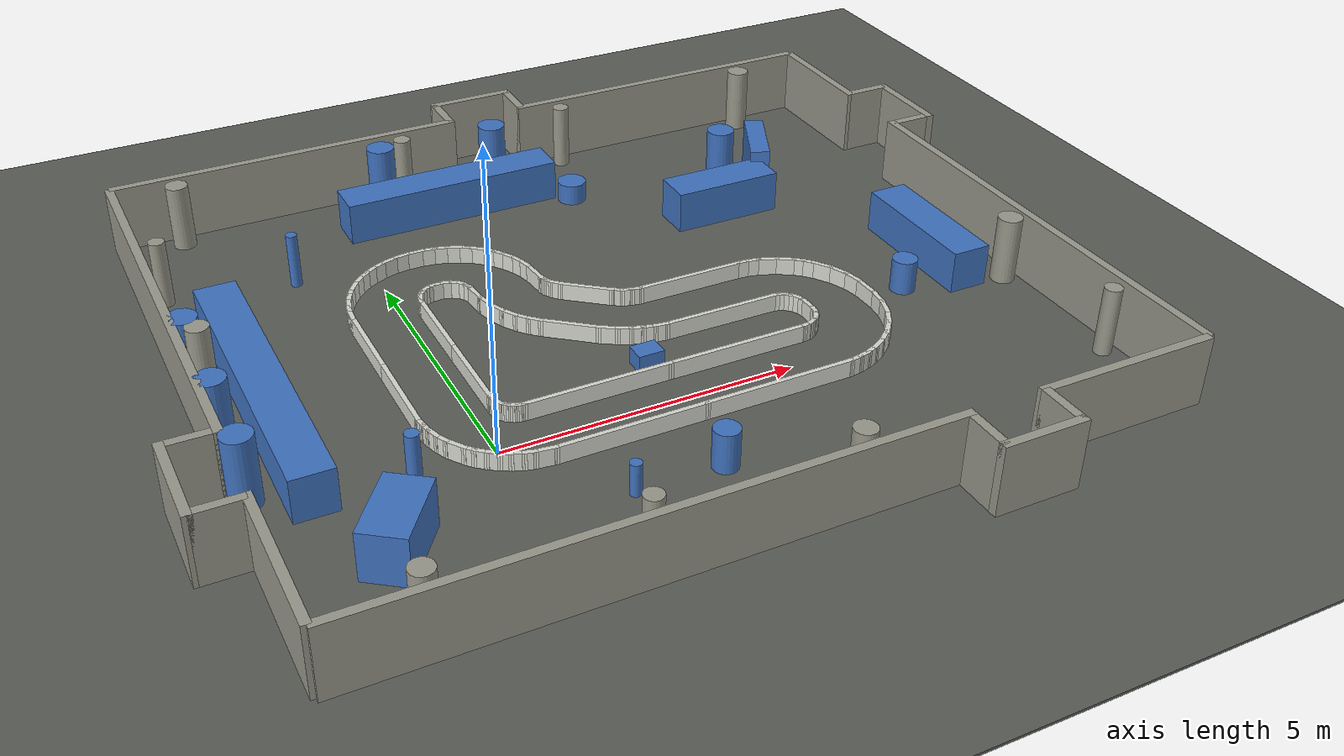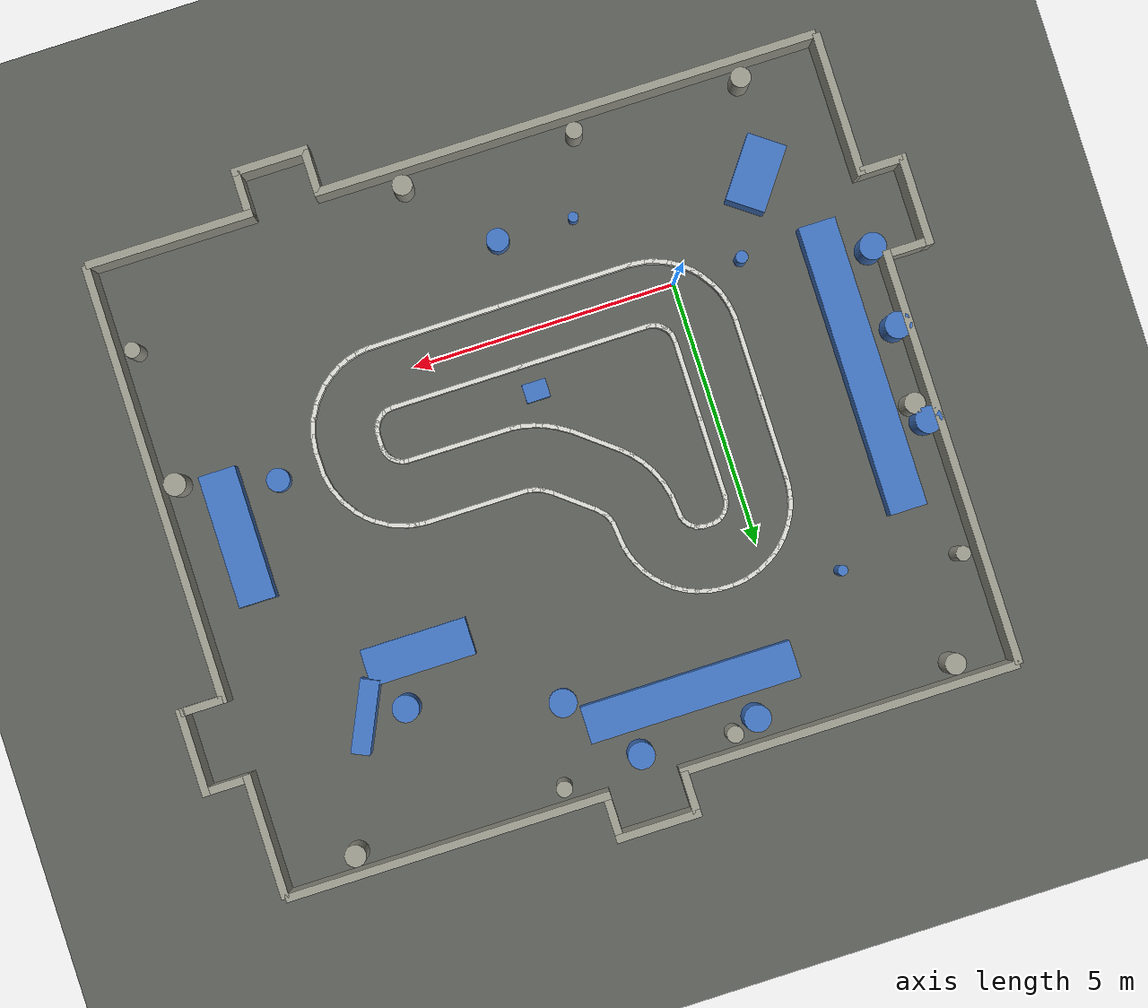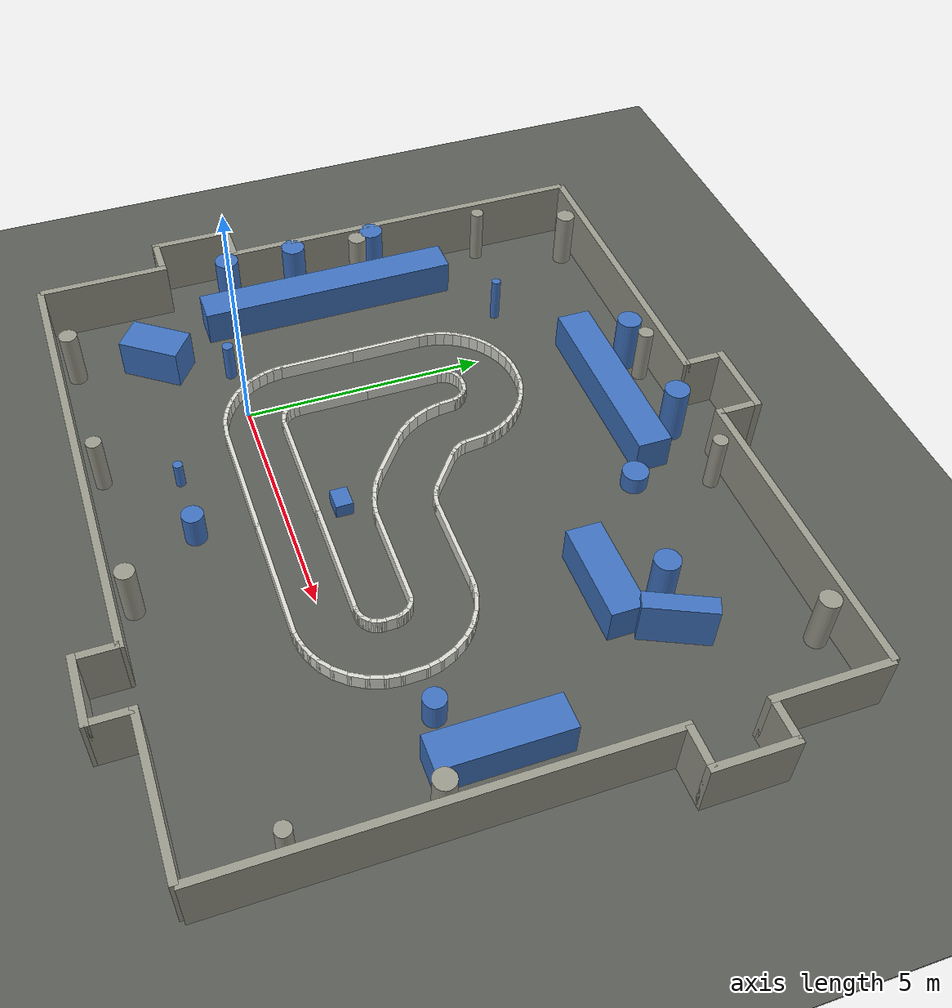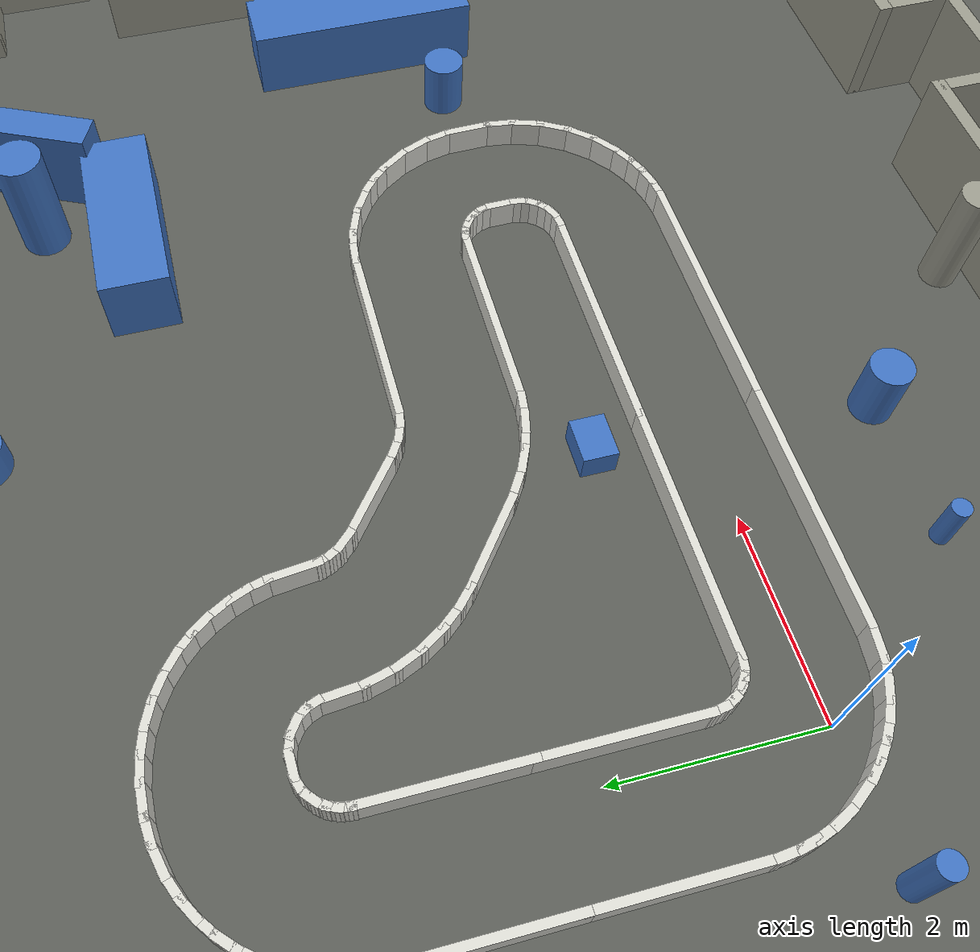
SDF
<?xml version="1.0" ?>
<sdf version="1.9">
  <world name="default">
    <physics name="default_physics" type="dart">
      <max_step_size>0.001</max_step_size>
      <real_time_factor>1.0</real_time_factor>
      <real_time_update_rate>1000.0</real_time_update_rate>
    </physics>
    <plugin filename="gz-sim-physics-system" name="gz::sim::systems::Physics" />
    <plugin filename="gz-sim-user-commands-system" name="gz::sim::systems::UserCommands" />
    <plugin filename="gz-sim-scene-broadcaster-system" name="gz::sim::systems::SceneBroadcaster" />
    <plugin filename="gz-sim-imu-system" name="gz::sim::systems::Imu" />
    <plugin filename="gz-sim-sensors-system" name="gz::sim::systems::Sensors">
      <render_engine>ogre2</render_engine>
    </plugin>
    <light type="directional" name="sun">
      <pose>0 0 10 0 0 0</pose>
      <diffuse>0.8 0.8 0.8 1</diffuse>
      <direction>-0.5 0.5 -1</direction>
      <cast_shadows>true</cast_shadows>
    </light>
    <model name="track_feature">
      <static>true</static>
      <pose>0 0 0 0 0 0</pose>
      <link name="feature_link">
        <collision name="feat_box_2_collision">
          <pose>7.757710 5.823984 0.472198 0.000000 0.000000 1.136605</pose>
          <geometry>
            <box>
              <size>1.369153 0.357167 0.944397</size>
            </box>
          </geometry>
        </collision>
        <visual name="feat_box_2_visual">
          <pose>7.757710 5.823984 0.472198 0.000000 0.000000 1.136605</pose>
          <geometry>
            <box>
              <size>1.369153 0.357167 0.944397</size>
            </box>
          </geometry>
          <material>
            <ambient>0.25 0.45 0.75 1</ambient>
            <diffuse>0.25 0.45 0.75 1</diffuse>
          </material>
        </visual>
        <collision name="feat_box_6_collision">
          <pose>-2.024471 -1.446810 0.414715 0.000000 0.000000 0.939065</pose>
          <geometry>
            <box>
              <size>1.286521 0.748022 0.829431</size>
            </box>
          </geometry>
        </collision>
        <visual name="feat_box_6_visual">
          <pose>-2.024471 -1.446810 0.414715 0.000000 0.000000 0.939065</pose>
          <geometry>
            <box>
              <size>1.286521 0.748022 0.829431</size>
            </box>
          </geometry>
          <material>
            <ambient>0.25 0.45 0.75 1</ambient>
            <diffuse>0.25 0.45 0.75 1</diffuse>
          </material>
        </visual>
        <collision name="landmark_0_collision">
          <pose>-2.800000 2.500000 0.375000 0.000000 0.000000 0.000000</pose>
          <geometry>
            <box>
              <size>0.700000 5.500000 0.750000</size>
            </box>
          </geometry>
        </collision>
        <visual name="landmark_0_visual">
          <pose>-2.800000 2.500000 0.375000 0.000000 0.000000 0.000000</pose>
          <geometry>
            <box>
              <size>0.700000 5.500000 0.750000</size>
            </box>
          </geometry>
          <material>
            <ambient>0.25 0.45 0.75 1</ambient>
            <diffuse>0.25 0.45 0.75 1</diffuse>
          </material>
        </visual>
        <collision name="landmark_1_collision">
          <pose>2.000000 7.200000 0.375000 0.000000 0.000000 0.000000</pose>
          <geometry>
            <box>
              <size>4.000000 0.700000 0.750000</size>
            </box>
          </geometry>
        </collision>
        <visual name="landmark_1_visual">
          <pose>2.000000 7.200000 0.375000 0.000000 0.000000 0.000000</pose>
          <geometry>
            <box>
              <size>4.000000 0.700000 0.750000</size>
            </box>
          </geometry>
          <material>
            <ambient>0.25 0.45 0.75 1</ambient>
            <diffuse>0.25 0.45 0.75 1</diffuse>
          </material>
        </visual>
        <collision name="landmark_2_collision">
          <pose>6.500000 5.000000 0.375000 0.000000 0.000000 0.000000</pose>
          <geometry>
            <box>
              <size>2.000000 0.700000 0.750000</size>
            </box>
          </geometry>
        </collision>
        <visual name="landmark_2_visual">
          <pose>6.500000 5.000000 0.375000 0.000000 0.000000 0.000000</pose>
          <geometry>
            <box>
              <size>2.000000 0.700000 0.750000</size>
            </box>
          </geometry>
          <material>
            <ambient>0.25 0.45 0.75 1</ambient>
            <diffuse>0.25 0.45 0.75 1</diffuse>
          </material>
        </visual>
        <collision name="landmark_3_collision">
          <pose>9.000000 2.000000 0.375000 0.000000 0.000000 0.000000</pose>
          <geometry>
            <box>
              <size>0.700000 2.500000 0.750000</size>
            </box>
          </geometry>
        </collision>
        <visual name="landmark_3_visual">
          <pose>9.000000 2.000000 0.375000 0.000000 0.000000 0.000000</pose>
          <geometry>
            <box>
              <size>0.700000 2.500000 0.750000</size>
            </box>
          </geometry>
          <material>
            <ambient>0.25 0.45 0.75 1</ambient>
            <diffuse>0.25 0.45 0.75 1</diffuse>
          </material>
        </visual>
        <collision name="landmark_10_collision">
          <pose>3.000000 1.100000 0.150000 0.000000 0.000000 0.000000</pose>
          <geometry>
            <box>
              <size>0.450000 0.350000 0.300000</size>
            </box>
          </geometry>
        </collision>
        <visual name="landmark_10_visual">
          <pose>3.000000 1.100000 0.150000 0.000000 0.000000 0.000000</pose>
          <geometry>
            <box>
              <size>0.450000 0.350000 0.300000</size>
            </box>
          </geometry>
          <material>
            <ambient>0.25 0.45 0.75 1</ambient>
            <diffuse>0.25 0.45 0.75 1</diffuse>
          </material>
        </visual>
        <collision name="feat_cyl_1_collision">
          <pose>7.984504 1.234789 0.300090 0.000000 0.000000 0.000000</pose>
          <geometry>
            <cylinder>
              <radius>0.217820</radius>
              <length>0.600179</length>
            </cylinder>
          </geometry>
        </collision>
        <visual name="feat_cyl_1_visual">
          <pose>7.984504 1.234789 0.300090 0.000000 0.000000 0.000000</pose>
          <geometry>
            <cylinder>
              <radius>0.217820</radius>
              <length>0.600179</length>
            </cylinder>
          </geometry>
          <material>
            <ambient>0.25 0.45 0.75 1</ambient>
            <diffuse>0.25 0.45 0.75 1</diffuse>
          </material>
        </visual>
        <collision name="feat_cyl_3_collision">
          <pose>2.834560 -1.722751 0.340881 0.000000 0.000000 0.000000</pose>
          <geometry>
            <cylinder>
              <radius>0.213408</radius>
              <length>0.681762</length>
            </cylinder>
          </geometry>
        </collision>
        <visual name="feat_cyl_3_visual">
          <pose>2.834560 -1.722751 0.340881 0.000000 0.000000 0.000000</pose>
          <geometry>
            <cylinder>
              <radius>0.213408</radius>
              <length>0.681762</length>
            </cylinder>
          </geometry>
          <material>
            <ambient>0.25 0.45 0.75 1</ambient>
            <diffuse>0.25 0.45 0.75 1</diffuse>
          </material>
        </visual>
        <collision name="feat_cyl_4_collision">
          <pose>-1.305083 -0.057571 0.416565 0.000000 0.000000 0.000000</pose>
          <geometry>
            <cylinder>
              <radius>0.114796</radius>
              <length>0.833129</length>
            </cylinder>
          </geometry>
        </collision>
        <visual name="feat_cyl_4_visual">
          <pose>-1.305083 -0.057571 0.416565 0.000000 0.000000 0.000000</pose>
          <geometry>
            <cylinder>
              <radius>0.114796</radius>
              <length>0.833129</length>
            </cylinder>
          </geometry>
          <material>
            <ambient>0.25 0.45 0.75 1</ambient>
            <diffuse>0.25 0.45 0.75 1</diffuse>
          </material>
        </visual>
        <collision name="feat_cyl_5_collision">
          <pose>4.268548 6.696389 0.189830 0.000000 0.000000 0.000000</pose>
          <geometry>
            <cylinder>
              <radius>0.263632</radius>
              <length>0.379660</length>
            </cylinder>
          </geometry>
        </collision>
        <visual name="feat_cyl_5_visual">
          <pose>4.268548 6.696389 0.189830 0.000000 0.000000 0.000000</pose>
          <geometry>
            <cylinder>
              <radius>0.263632</radius>
              <length>0.379660</length>
            </cylinder>
          </geometry>
          <material>
            <ambient>0.25 0.45 0.75 1</ambient>
            <diffuse>0.25 0.45 0.75 1</diffuse>
          </material>
        </visual>
        <collision name="feat_cyl_7_collision">
          <pose>-1.298939 5.929700 0.489099 0.000000 0.000000 0.000000</pose>
          <geometry>
            <cylinder>
              <radius>0.096327</radius>
              <length>0.978199</length>
            </cylinder>
          </geometry>
        </collision>
        <visual name="feat_cyl_7_visual">
          <pose>-1.298939 5.929700 0.489099 0.000000 0.000000 0.000000</pose>
          <geometry>
            <cylinder>
              <radius>0.096327</radius>
              <length>0.978199</length>
            </cylinder>
          </geometry>
          <material>
            <ambient>0.25 0.45 0.75 1</ambient>
            <diffuse>0.25 0.45 0.75 1</diffuse>
          </material>
        </visual>
        <collision name="feat_cyl_8_collision">
          <pose>1.389119 -1.712532 0.274791 0.000000 0.000000 0.000000</pose>
          <geometry>
            <cylinder>
              <radius>0.094864</radius>
              <length>0.549582</length>
            </cylinder>
          </geometry>
        </collision>
        <visual name="feat_cyl_8_visual">
          <pose>1.389119 -1.712532 0.274791 0.000000 0.000000 0.000000</pose>
          <geometry>
            <cylinder>
              <radius>0.094864</radius>
              <length>0.549582</length>
            </cylinder>
          </geometry>
          <material>
            <ambient>0.25 0.45 0.75 1</ambient>
            <diffuse>0.25 0.45 0.75 1</diffuse>
          </material>
        </visual>
        <collision name="landmark_4_collision">
          <pose>-3.600000 0.500000 0.600000 0.000000 0.000000 0.000000</pose>
          <geometry>
            <cylinder>
              <radius>0.250000</radius>
              <length>1.200000</length>
            </cylinder>
          </geometry>
        </collision>
        <visual name="landmark_4_visual">
          <pose>-3.600000 0.500000 0.600000 0.000000 0.000000 0.000000</pose>
          <geometry>
            <cylinder>
              <radius>0.250000</radius>
              <length>1.200000</length>
            </cylinder>
          </geometry>
          <material>
            <ambient>0.25 0.45 0.75 1</ambient>
            <diffuse>0.25 0.45 0.75 1</diffuse>
          </material>
        </visual>
        <collision name="landmark_5_collision">
          <pose>-3.600000 2.000000 0.600000 0.000000 0.000000 0.000000</pose>
          <geometry>
            <cylinder>
              <radius>0.250000</radius>
              <length>1.200000</length>
            </cylinder>
          </geometry>
        </collision>
        <visual name="landmark_5_visual">
          <pose>-3.600000 2.000000 0.600000 0.000000 0.000000 0.000000</pose>
          <geometry>
            <cylinder>
              <radius>0.250000</radius>
              <length>1.200000</length>
            </cylinder>
          </geometry>
          <material>
            <ambient>0.25 0.45 0.75 1</ambient>
            <diffuse>0.25 0.45 0.75 1</diffuse>
          </material>
        </visual>
        <collision name="landmark_6_collision">
          <pose>-3.600000 3.800000 0.600000 0.000000 0.000000 0.000000</pose>
          <geometry>
            <cylinder>
              <radius>0.250000</radius>
              <length>1.200000</length>
            </cylinder>
          </geometry>
        </collision>
        <visual name="landmark_6_visual">
          <pose>-3.600000 3.800000 0.600000 0.000000 0.000000 0.000000</pose>
          <geometry>
            <cylinder>
              <radius>0.250000</radius>
              <length>1.200000</length>
            </cylinder>
          </geometry>
          <material>
            <ambient>0.25 0.45 0.75 1</ambient>
            <diffuse>0.25 0.45 0.75 1</diffuse>
          </material>
        </visual>
        <collision name="landmark_7_collision">
          <pose>1.000000 8.000000 0.600000 0.000000 0.000000 0.000000</pose>
          <geometry>
            <cylinder>
              <radius>0.250000</radius>
              <length>1.200000</length>
            </cylinder>
          </geometry>
        </collision>
        <visual name="landmark_7_visual">
          <pose>1.000000 8.000000 0.600000 0.000000 0.000000 0.000000</pose>
          <geometry>
            <cylinder>
              <radius>0.250000</radius>
              <length>1.200000</length>
            </cylinder>
          </geometry>
          <material>
            <ambient>0.25 0.45 0.75 1</ambient>
            <diffuse>0.25 0.45 0.75 1</diffuse>
          </material>
        </visual>
        <collision name="landmark_8_collision">
          <pose>3.200000 8.000000 0.600000 0.000000 0.000000 0.000000</pose>
          <geometry>
            <cylinder>
              <radius>0.250000</radius>
              <length>1.200000</length>
            </cylinder>
          </geometry>
        </collision>
        <visual name="landmark_8_visual">
          <pose>3.200000 8.000000 0.600000 0.000000 0.000000 0.000000</pose>
          <geometry>
            <cylinder>
              <radius>0.250000</radius>
              <length>1.200000</length>
            </cylinder>
          </geometry>
          <material>
            <ambient>0.25 0.45 0.75 1</ambient>
            <diffuse>0.25 0.45 0.75 1</diffuse>
          </material>
        </visual>
        <collision name="landmark_9_collision">
          <pose>7.000000 5.900000 0.600000 0.000000 0.000000 0.000000</pose>
          <geometry>
            <cylinder>
              <radius>0.250000</radius>
              <length>1.200000</length>
            </cylinder>
          </geometry>
        </collision>
        <visual name="landmark_9_visual">
          <pose>7.000000 5.900000 0.600000 0.000000 0.000000 0.000000</pose>
          <geometry>
            <cylinder>
              <radius>0.250000</radius>
              <length>1.200000</length>
            </cylinder>
          </geometry>
          <material>
            <ambient>0.25 0.45 0.75 1</ambient>
            <diffuse>0.25 0.45 0.75 1</diffuse>
          </material>
        </visual>
      </link>
    </model>
    <model name="track_ground">
      <static>true</static>
      <pose>0 0 0 0 0 0</pose>
      <link name="ground_link">
        <collision name="ground_collision">
          <pose>2.604407 1.885509 -0.025000 0.000000 0.000000 0.000000</pose>
          <geometry>
            <box>
              <size>80.000000 80.000000 0.050000</size>
            </box>
          </geometry>
          <surface>
            <friction>
              <ode>
                <mu>1.2</mu>
                <mu2>1.2</mu2>
              </ode>
            </friction>
            <contact>
              <ode>
                <kp>100000.0</kp>
                <kd>10.0</kd>
              </ode>
            </contact>
          </surface>
        </collision>
        <visual name="ground_visual">
          <pose>2.604407 1.885509 -0.025000 0.000000 0.000000 0.000000</pose>
          <geometry>
            <box>
              <size>80.000000 80.000000 0.050000</size>
            </box>
          </geometry>
          <material>
            <ambient>0.35 0.36 0.34 1</ambient>
            <diffuse>0.35 0.36 0.34 1</diffuse>
          </material>
        </visual>
      </link>
    </model>
    <model name="track_room">
      <static>true</static>
      <pose>0 0 0 0 0 0</pose>
      <link name="room_link">
        <collision name="hall_0_0_collision">
          <pose>0.978934 -3.500000 0.600000 0.000000 0.000000 0.000000</pose>
          <geometry>
            <box>
              <size>9.557868 0.150000 1.200000</size>
            </box>
          </geometry>
        </collision>
        <visual name="hall_0_0_visual">
          <pose>0.978934 -3.500000 0.600000 0.000000 0.000000 0.000000</pose>
          <geometry>
            <box>
              <size>9.557868 0.150000 1.200000</size>
            </box>
          </geometry>
          <material>
            <ambient>0.6 0.6 0.55 1</ambient>
            <diffuse>0.6 0.6 0.55 1</diffuse>
          </material>
        </visual>
        <collision name="hall_0_107_collision">
          <pose>8.510477 -3.500000 0.600000 0.000000 0.000000 0.000000</pose>
          <geometry>
            <box>
              <size>3.179045 0.150000 1.200000</size>
            </box>
          </geometry>
        </collision>
        <visual name="hall_0_107_visual">
          <pose>8.510477 -3.500000 0.600000 0.000000 0.000000 0.000000</pose>
          <geometry>
            <box>
              <size>3.179045 0.150000 1.200000</size>
            </box>
          </geometry>
          <material>
            <ambient>0.6 0.6 0.55 1</ambient>
            <diffuse>0.6 0.6 0.55 1</diffuse>
          </material>
        </visual>
        <collision name="hall_niche_0_collision">
          <pose>6.339411 -4.300000 0.600000 0.000000 0.000000 0.000000</pose>
          <geometry>
            <box>
              <size>1.463087 0.150000 1.200000</size>
            </box>
          </geometry>
        </collision>
        <visual name="hall_niche_0_visual">
          <pose>6.339411 -4.300000 0.600000 0.000000 0.000000 0.000000</pose>
          <geometry>
            <box>
              <size>1.463087 0.150000 1.200000</size>
            </box>
          </geometry>
          <material>
            <ambient>0.6 0.6 0.55 1</ambient>
            <diffuse>0.6 0.6 0.55 1</diffuse>
          </material>
        </visual>
        <collision name="hall_jamb_0_-1_collision">
          <pose>5.682868 -3.900000 0.600000 0.000000 0.000000 0.000000</pose>
          <geometry>
            <box>
              <size>0.150000 0.800000 1.200000</size>
            </box>
          </geometry>
        </collision>
        <visual name="hall_jamb_0_-1_visual">
          <pose>5.682868 -3.900000 0.600000 0.000000 0.000000 0.000000</pose>
          <geometry>
            <box>
              <size>0.150000 0.800000 1.200000</size>
            </box>
          </geometry>
          <material>
            <ambient>0.6 0.6 0.55 1</ambient>
            <diffuse>0.6 0.6 0.55 1</diffuse>
          </material>
        </visual>
        <collision name="hall_jamb_0_1_collision">
          <pose>6.995955 -3.900000 0.600000 0.000000 0.000000 0.000000</pose>
          <geometry>
            <box>
              <size>0.150000 0.800000 1.200000</size>
            </box>
          </geometry>
        </collision>
        <visual name="hall_jamb_0_1_visual">
          <pose>6.995955 -3.900000 0.600000 0.000000 0.000000 0.000000</pose>
          <geometry>
            <box>
              <size>0.150000 0.800000 1.200000</size>
            </box>
          </geometry>
          <material>
            <ambient>0.6 0.6 0.55 1</ambient>
            <diffuse>0.6 0.6 0.55 1</diffuse>
          </material>
        </visual>
        <collision name="hall_1_0_collision">
          <pose>10.100000 0.654623 0.600000 0.000000 0.000000 1.570796</pose>
          <geometry>
            <box>
              <size>8.309245 0.150000 1.200000</size>
            </box>
          </geometry>
        </collision>
        <visual name="hall_1_0_visual">
          <pose>10.100000 0.654623 0.600000 0.000000 0.000000 1.570796</pose>
          <geometry>
            <box>
              <size>8.309245 0.150000 1.200000</size>
            </box>
          </geometry>
          <material>
            <ambient>0.6 0.6 0.55 1</ambient>
            <diffuse>0.6 0.6 0.55 1</diffuse>
          </material>
        </visual>
        <collision name="hall_1_96_collision">
          <pose>10.100000 7.328956 0.600000 0.000000 0.000000 1.570796</pose>
          <geometry>
            <box>
              <size>2.342089 0.150000 1.200000</size>
            </box>
          </geometry>
        </collision>
        <visual name="hall_1_96_visual">
          <pose>10.100000 7.328956 0.600000 0.000000 0.000000 1.570796</pose>
          <geometry>
            <box>
              <size>2.342089 0.150000 1.200000</size>
            </box>
          </geometry>
          <material>
            <ambient>0.6 0.6 0.55 1</ambient>
            <diffuse>0.6 0.6 0.55 1</diffuse>
          </material>
        </visual>
        <collision name="hall_niche_1_collision">
          <pose>10.900000 5.483578 0.600000 0.000000 0.000000 1.570796</pose>
          <geometry>
            <box>
              <size>1.648666 0.150000 1.200000</size>
            </box>
          </geometry>
        </collision>
        <visual name="hall_niche_1_visual">
          <pose>10.900000 5.483578 0.600000 0.000000 0.000000 1.570796</pose>
          <geometry>
            <box>
              <size>1.648666 0.150000 1.200000</size>
            </box>
          </geometry>
          <material>
            <ambient>0.6 0.6 0.55 1</ambient>
            <diffuse>0.6 0.6 0.55 1</diffuse>
          </material>
        </visual>
        <collision name="hall_jamb_1_-1_collision">
          <pose>10.500000 4.734245 0.600000 0.000000 0.000000 1.570796</pose>
          <geometry>
            <box>
              <size>0.150000 0.800000 1.200000</size>
            </box>
          </geometry>
        </collision>
        <visual name="hall_jamb_1_-1_visual">
          <pose>10.500000 4.734245 0.600000 0.000000 0.000000 1.570796</pose>
          <geometry>
            <box>
              <size>0.150000 0.800000 1.200000</size>
            </box>
          </geometry>
          <material>
            <ambient>0.6 0.6 0.55 1</ambient>
            <diffuse>0.6 0.6 0.55 1</diffuse>
          </material>
        </visual>
        <collision name="hall_jamb_1_1_collision">
          <pose>10.500000 6.232911 0.600000 0.000000 0.000000 1.570796</pose>
          <geometry>
            <box>
              <size>0.150000 0.800000 1.200000</size>
            </box>
          </geometry>
        </collision>
        <visual name="hall_jamb_1_1_visual">
          <pose>10.500000 6.232911 0.600000 0.000000 0.000000 1.570796</pose>
          <geometry>
            <box>
              <size>0.150000 0.800000 1.200000</size>
            </box>
          </geometry>
          <material>
            <ambient>0.6 0.6 0.55 1</ambient>
            <diffuse>0.6 0.6 0.55 1</diffuse>
          </material>
        </visual>
        <collision name="hall_2_0_collision">
          <pose>7.025139 8.500000 0.600000 0.000000 0.000000 3.141593</pose>
          <geometry>
            <box>
              <size>6.149723 0.150000 1.200000</size>
            </box>
          </geometry>
        </collision>
        <visual name="hall_2_0_visual">
          <pose>7.025139 8.500000 0.600000 0.000000 0.000000 3.141593</pose>
          <geometry>
            <box>
              <size>6.149723 0.150000 1.200000</size>
            </box>
          </geometry>
          <material>
            <ambient>0.6 0.6 0.55 1</ambient>
            <diffuse>0.6 0.6 0.55 1</diffuse>
          </material>
        </visual>
        <collision name="hall_2_74_collision">
          <pose>-0.582514 8.500000 0.600000 0.000000 0.000000 3.141593</pose>
          <geometry>
            <box>
              <size>6.434973 0.150000 1.200000</size>
            </box>
          </geometry>
        </collision>
        <visual name="hall_2_74_visual">
          <pose>-0.582514 8.500000 0.600000 0.000000 0.000000 3.141593</pose>
          <geometry>
            <box>
              <size>6.434973 0.150000 1.200000</size>
            </box>
          </geometry>
          <material>
            <ambient>0.6 0.6 0.55 1</ambient>
            <diffuse>0.6 0.6 0.55 1</diffuse>
          </material>
        </visual>
        <collision name="hall_niche_2_collision">
          <pose>3.292625 9.300000 0.600000 0.000000 0.000000 3.141593</pose>
          <geometry>
            <box>
              <size>1.615304 0.150000 1.200000</size>
            </box>
          </geometry>
        </collision>
        <visual name="hall_niche_2_visual">
          <pose>3.292625 9.300000 0.600000 0.000000 0.000000 3.141593</pose>
          <geometry>
            <box>
              <size>1.615304 0.150000 1.200000</size>
            </box>
          </geometry>
          <material>
            <ambient>0.6 0.6 0.55 1</ambient>
            <diffuse>0.6 0.6 0.55 1</diffuse>
          </material>
        </visual>
        <collision name="hall_jamb_2_-1_collision">
          <pose>4.025277 8.900000 0.600000 0.000000 0.000000 3.141593</pose>
          <geometry>
            <box>
              <size>0.150000 0.800000 1.200000</size>
            </box>
          </geometry>
        </collision>
        <visual name="hall_jamb_2_-1_visual">
          <pose>4.025277 8.900000 0.600000 0.000000 0.000000 3.141593</pose>
          <geometry>
            <box>
              <size>0.150000 0.800000 1.200000</size>
            </box>
          </geometry>
          <material>
            <ambient>0.6 0.6 0.55 1</ambient>
            <diffuse>0.6 0.6 0.55 1</diffuse>
          </material>
        </visual>
        <collision name="hall_jamb_2_1_collision">
          <pose>2.559973 8.900000 0.600000 0.000000 0.000000 3.141593</pose>
          <geometry>
            <box>
              <size>0.150000 0.800000 1.200000</size>
            </box>
          </geometry>
        </collision>
        <visual name="hall_jamb_2_1_visual">
          <pose>2.559973 8.900000 0.600000 0.000000 0.000000 3.141593</pose>
          <geometry>
            <box>
              <size>0.150000 0.800000 1.200000</size>
            </box>
          </geometry>
          <material>
            <ambient>0.6 0.6 0.55 1</ambient>
            <diffuse>0.6 0.6 0.55 1</diffuse>
          </material>
        </visual>
        <collision name="hall_3_0_collision">
          <pose>-3.800000 4.570141 0.600000 0.000000 0.000000 -1.570796</pose>
          <geometry>
            <box>
              <size>7.859719 0.150000 1.200000</size>
            </box>
          </geometry>
        </collision>
        <visual name="hall_3_0_visual">
          <pose>-3.800000 4.570141 0.600000 0.000000 0.000000 -1.570796</pose>
          <geometry>
            <box>
              <size>7.859719 0.150000 1.200000</size>
            </box>
          </geometry>
          <material>
            <ambient>0.6 0.6 0.55 1</ambient>
            <diffuse>0.6 0.6 0.55 1</diffuse>
          </material>
        </visual>
        <collision name="hall_3_92_collision">
          <pose>-3.800000 -2.143455 0.600000 0.000000 0.000000 -1.570796</pose>
          <geometry>
            <box>
              <size>2.713090 0.150000 1.200000</size>
            </box>
          </geometry>
        </collision>
        <visual name="hall_3_92_visual">
          <pose>-3.800000 -2.143455 0.600000 0.000000 0.000000 -1.570796</pose>
          <geometry>
            <box>
              <size>2.713090 0.150000 1.200000</size>
            </box>
          </geometry>
          <material>
            <ambient>0.6 0.6 0.55 1</ambient>
            <diffuse>0.6 0.6 0.55 1</diffuse>
          </material>
        </visual>
        <collision name="hall_niche_3_collision">
          <pose>-4.600000 -0.073314 0.600000 0.000000 0.000000 -1.570796</pose>
          <geometry>
            <box>
              <size>1.727191 0.150000 1.200000</size>
            </box>
          </geometry>
        </collision>
        <visual name="hall_niche_3_visual">
          <pose>-4.600000 -0.073314 0.600000 0.000000 0.000000 -1.570796</pose>
          <geometry>
            <box>
              <size>1.727191 0.150000 1.200000</size>
            </box>
          </geometry>
          <material>
            <ambient>0.6 0.6 0.55 1</ambient>
            <diffuse>0.6 0.6 0.55 1</diffuse>
          </material>
        </visual>
        <collision name="hall_jamb_3_-1_collision">
          <pose>-4.200000 0.715281 0.600000 0.000000 0.000000 -1.570796</pose>
          <geometry>
            <box>
              <size>0.150000 0.800000 1.200000</size>
            </box>
          </geometry>
        </collision>
        <visual name="hall_jamb_3_-1_visual">
          <pose>-4.200000 0.715281 0.600000 0.000000 0.000000 -1.570796</pose>
          <geometry>
            <box>
              <size>0.150000 0.800000 1.200000</size>
            </box>
          </geometry>
          <material>
            <ambient>0.6 0.6 0.55 1</ambient>
            <diffuse>0.6 0.6 0.55 1</diffuse>
          </material>
        </visual>
        <collision name="hall_jamb_3_1_collision">
          <pose>-4.200000 -0.861910 0.600000 0.000000 0.000000 -1.570796</pose>
          <geometry>
            <box>
              <size>0.150000 0.800000 1.200000</size>
            </box>
          </geometry>
        </collision>
        <visual name="hall_jamb_3_1_visual">
          <pose>-4.200000 -0.861910 0.600000 0.000000 0.000000 -1.570796</pose>
          <geometry>
            <box>
              <size>0.150000 0.800000 1.200000</size>
            </box>
          </geometry>
          <material>
            <ambient>0.6 0.6 0.55 1</ambient>
            <diffuse>0.6 0.6 0.55 1</diffuse>
          </material>
        </visual>
        <collision name="column_0_15_collision">
          <pose>-2.256256 -3.150000 0.600000 0.000000 0.000000 0.000000</pose>
          <geometry>
            <cylinder>
              <radius>0.188989</radius>
              <length>1.200000</length>
            </cylinder>
          </geometry>
        </collision>
        <visual name="column_0_15_visual">
          <pose>-2.256256 -3.150000 0.600000 0.000000 0.000000 0.000000</pose>
          <geometry>
            <cylinder>
              <radius>0.188989</radius>
              <length>1.200000</length>
            </cylinder>
          </geometry>
          <material>
            <ambient>0.6 0.6 0.55 1</ambient>
            <diffuse>0.6 0.6 0.55 1</diffuse>
          </material>
        </visual>
        <collision name="column_0_47_collision">
          <pose>0.918113 -3.150000 0.600000 0.000000 0.000000 0.000000</pose>
          <geometry>
            <cylinder>
              <radius>0.156819</radius>
              <length>1.200000</length>
            </cylinder>
          </geometry>
        </collision>
        <visual name="column_0_47_visual">
          <pose>0.918113 -3.150000 0.600000 0.000000 0.000000 0.000000</pose>
          <geometry>
            <cylinder>
              <radius>0.156819</radius>
              <length>1.200000</length>
            </cylinder>
          </geometry>
          <material>
            <ambient>0.6 0.6 0.55 1</ambient>
            <diffuse>0.6 0.6 0.55 1</diffuse>
          </material>
        </visual>
        <collision name="column_0_79_collision">
          <pose>4.186807 -3.150000 0.600000 0.000000 0.000000 0.000000</pose>
          <geometry>
            <cylinder>
              <radius>0.189532</radius>
              <length>1.200000</length>
            </cylinder>
          </geometry>
        </collision>
        <visual name="column_0_79_visual">
          <pose>4.186807 -3.150000 0.600000 0.000000 0.000000 0.000000</pose>
          <geometry>
            <cylinder>
              <radius>0.189532</radius>
              <length>1.200000</length>
            </cylinder>
          </geometry>
          <material>
            <ambient>0.6 0.6 0.55 1</ambient>
            <diffuse>0.6 0.6 0.55 1</diffuse>
          </material>
        </visual>
        <collision name="column_1_17_collision">
          <pose>9.750000 -1.787275 0.600000 0.000000 0.000000 0.000000</pose>
          <geometry>
            <cylinder>
              <radius>0.148920</radius>
              <length>1.200000</length>
            </cylinder>
          </geometry>
        </collision>
        <visual name="column_1_17_visual">
          <pose>9.750000 -1.787275 0.600000 0.000000 0.000000 0.000000</pose>
          <geometry>
            <cylinder>
              <radius>0.148920</radius>
              <length>1.200000</length>
            </cylinder>
          </geometry>
          <material>
            <ambient>0.6 0.6 0.55 1</ambient>
            <diffuse>0.6 0.6 0.55 1</diffuse>
          </material>
        </visual>
        <collision name="column_1_42_collision">
          <pose>9.750000 0.769416 0.600000 0.000000 0.000000 0.000000</pose>
          <geometry>
            <cylinder>
              <radius>0.210949</radius>
              <length>1.200000</length>
            </cylinder>
          </geometry>
        </collision>
        <visual name="column_1_42_visual">
          <pose>9.750000 0.769416 0.600000 0.000000 0.000000 0.000000</pose>
          <geometry>
            <cylinder>
              <radius>0.210949</radius>
              <length>1.200000</length>
            </cylinder>
          </geometry>
          <material>
            <ambient>0.6 0.6 0.55 1</ambient>
            <diffuse>0.6 0.6 0.55 1</diffuse>
          </material>
        </visual>
        <collision name="column_2_14_collision">
          <pose>8.666504 8.150000 0.600000 0.000000 0.000000 0.000000</pose>
          <geometry>
            <cylinder>
              <radius>0.202840</radius>
              <length>1.200000</length>
            </cylinder>
          </geometry>
        </collision>
        <visual name="column_2_14_visual">
          <pose>8.666504 8.150000 0.600000 0.000000 0.000000 0.000000</pose>
          <geometry>
            <cylinder>
              <radius>0.202840</radius>
              <length>1.200000</length>
            </cylinder>
          </geometry>
          <material>
            <ambient>0.6 0.6 0.55 1</ambient>
            <diffuse>0.6 0.6 0.55 1</diffuse>
          </material>
        </visual>
        <collision name="column_2_53_collision">
          <pose>4.709868 8.150000 0.600000 0.000000 0.000000 0.000000</pose>
          <geometry>
            <cylinder>
              <radius>0.149667</radius>
              <length>1.200000</length>
            </cylinder>
          </geometry>
        </collision>
        <visual name="column_2_53_visual">
          <pose>4.709868 8.150000 0.600000 0.000000 0.000000 0.000000</pose>
          <geometry>
            <cylinder>
              <radius>0.149667</radius>
              <length>1.200000</length>
            </cylinder>
          </geometry>
          <material>
            <ambient>0.6 0.6 0.55 1</ambient>
            <diffuse>0.6 0.6 0.55 1</diffuse>
          </material>
        </visual>
        <collision name="column_2_86_collision">
          <pose>1.472220 8.150000 0.600000 0.000000 0.000000 0.000000</pose>
          <geometry>
            <cylinder>
              <radius>0.155623</radius>
              <length>1.200000</length>
            </cylinder>
          </geometry>
        </collision>
        <visual name="column_2_86_visual">
          <pose>1.472220 8.150000 0.600000 0.000000 0.000000 0.000000</pose>
          <geometry>
            <cylinder>
              <radius>0.155623</radius>
              <length>1.200000</length>
            </cylinder>
          </geometry>
          <material>
            <ambient>0.6 0.6 0.55 1</ambient>
            <diffuse>0.6 0.6 0.55 1</diffuse>
          </material>
        </visual>
        <collision name="column_2_128_collision">
          <pose>-2.704519 8.150000 0.600000 0.000000 0.000000 0.000000</pose>
          <geometry>
            <cylinder>
              <radius>0.196957</radius>
              <length>1.200000</length>
            </cylinder>
          </geometry>
        </collision>
        <visual name="column_2_128_visual">
          <pose>-2.704519 8.150000 0.600000 0.000000 0.000000 0.000000</pose>
          <geometry>
            <cylinder>
              <radius>0.196957</radius>
              <length>1.200000</length>
            </cylinder>
          </geometry>
          <material>
            <ambient>0.6 0.6 0.55 1</ambient>
            <diffuse>0.6 0.6 0.55 1</diffuse>
          </material>
        </visual>
        <collision name="column_3_22_collision">
          <pose>-3.450000 6.292686 0.600000 0.000000 0.000000 0.000000</pose>
          <geometry>
            <cylinder>
              <radius>0.139754</radius>
              <length>1.200000</length>
            </cylinder>
          </geometry>
        </collision>
        <visual name="column_3_22_visual">
          <pose>-3.450000 6.292686 0.600000 0.000000 0.000000 0.000000</pose>
          <geometry>
            <cylinder>
              <radius>0.139754</radius>
              <length>1.200000</length>
            </cylinder>
          </geometry>
          <material>
            <ambient>0.6 0.6 0.55 1</ambient>
            <diffuse>0.6 0.6 0.55 1</diffuse>
          </material>
        </visual>
        <collision name="column_3_50_collision">
          <pose>-3.450000 3.435501 0.600000 0.000000 0.000000 0.000000</pose>
          <geometry>
            <cylinder>
              <radius>0.193421</radius>
              <length>1.200000</length>
            </cylinder>
          </geometry>
        </collision>
        <visual name="column_3_50_visual">
          <pose>-3.450000 3.435501 0.600000 0.000000 0.000000 0.000000</pose>
          <geometry>
            <cylinder>
              <radius>0.193421</radius>
              <length>1.200000</length>
            </cylinder>
          </geometry>
          <material>
            <ambient>0.6 0.6 0.55 1</ambient>
            <diffuse>0.6 0.6 0.55 1</diffuse>
          </material>
        </visual>
      </link>
    </model>
    <model name="track_wall">
      <static>true</static>
      <pose>0 0 0 0 0 0</pose>
      <link name="wall_link">
        <collision name="left0_0_0_collision">
          <pose>4.373535 0.589996 0.150000 0.000000 0.000000 -0.000003</pose>
          <geometry>
            <box>
              <size>2.527070 0.080000 0.300000</size>
            </box>
          </geometry>
        </collision>
        <visual name="left0_0_0_visual">
          <pose>4.373535 0.589996 0.150000 0.000000 0.000000 -0.000003</pose>
          <geometry>
            <box>
              <size>2.527070 0.080000 0.300000</size>
            </box>
          </geometry>
          <material>
            <ambient>0.85 0.85 0.82 1</ambient>
            <diffuse>0.85 0.85 0.82 1</diffuse>
          </material>
        </visual>
        <collision name="left0_1_0_collision">
          <pose>5.658774 0.599047 0.150000 0.000000 0.000000 0.145694</pose>
          <geometry>
            <box>
              <size>0.204730 0.080000 0.300000</size>
            </box>
          </geometry>
        </collision>
        <visual name="left0_1_0_visual">
          <pose>5.658774 0.599047 0.150000 0.000000 0.000000 0.145694</pose>
          <geometry>
            <box>
              <size>0.204730 0.080000 0.300000</size>
            </box>
          </geometry>
          <material>
            <ambient>0.85 0.85 0.82 1</ambient>
            <diffuse>0.85 0.85 0.82 1</diffuse>
          </material>
        </visual>
        <collision name="left0_2_0_collision">
          <pose>5.768565 0.630009 0.150000 0.000000 0.000000 0.427495</pose>
          <geometry>
            <box>
              <size>0.185684 0.080000 0.300000</size>
            </box>
          </geometry>
        </collision>
        <visual name="left0_2_0_visual">
          <pose>5.768565 0.630009 0.150000 0.000000 0.000000 0.427495</pose>
          <geometry>
            <box>
              <size>0.185684 0.080000 0.300000</size>
            </box>
          </geometry>
          <material>
            <ambient>0.85 0.85 0.82 1</ambient>
            <diffuse>0.85 0.85 0.82 1</diffuse>
          </material>
        </visual>
        <collision name="left0_3_0_collision">
          <pose>5.857541 0.685389 0.150000 0.000000 0.000000 0.685981</pose>
          <geometry>
            <box>
              <size>0.185684 0.080000 0.300000</size>
            </box>
          </geometry>
        </collision>
        <visual name="left0_3_0_visual">
          <pose>5.857541 0.685389 0.150000 0.000000 0.000000 0.685981</pose>
          <geometry>
            <box>
              <size>0.185684 0.080000 0.300000</size>
            </box>
          </geometry>
          <material>
            <ambient>0.85 0.85 0.82 1</ambient>
            <diffuse>0.85 0.85 0.82 1</diffuse>
          </material>
        </visual>
        <collision name="left0_4_0_collision">
          <pose>5.929405 0.761672 0.150000 0.000000 0.000000 0.944466</pose>
          <geometry>
            <box>
              <size>0.185684 0.080000 0.300000</size>
            </box>
          </geometry>
        </collision>
        <visual name="left0_4_0_visual">
          <pose>5.929405 0.761672 0.150000 0.000000 0.000000 0.944466</pose>
          <geometry>
            <box>
              <size>0.185684 0.080000 0.300000</size>
            </box>
          </geometry>
          <material>
            <ambient>0.85 0.85 0.82 1</ambient>
            <diffuse>0.85 0.85 0.82 1</diffuse>
          </material>
        </visual>
        <collision name="left0_5_0_collision">
          <pose>5.978379 0.849841 0.150000 0.000000 0.000000 1.193010</pose>
          <geometry>
            <box>
              <size>0.177595 0.080000 0.300000</size>
            </box>
          </geometry>
        </collision>
        <visual name="left0_5_0_visual">
          <pose>5.978379 0.849841 0.150000 0.000000 0.000000 1.193010</pose>
          <geometry>
            <box>
              <size>0.177595 0.080000 0.300000</size>
            </box>
          </geometry>
          <material>
            <ambient>0.85 0.85 0.82 1</ambient>
            <diffuse>0.85 0.85 0.82 1</diffuse>
          </material>
        </visual>
        <collision name="left0_6_0_collision">
          <pose>6.003027 0.939449 0.150000 0.000000 0.000000 1.421670</pose>
          <geometry>
            <box>
              <size>0.169496 0.080000 0.300000</size>
            </box>
          </geometry>
        </collision>
        <visual name="left0_6_0_visual">
          <pose>6.003027 0.939449 0.150000 0.000000 0.000000 1.421670</pose>
          <geometry>
            <box>
              <size>0.169496 0.080000 0.300000</size>
            </box>
          </geometry>
          <material>
            <ambient>0.85 0.85 0.82 1</ambient>
            <diffuse>0.85 0.85 0.82 1</diffuse>
          </material>
        </visual>
        <collision name="left0_7_0_collision">
          <pose>6.008381 1.116249 0.150000 0.000000 0.000000 1.580566</pose>
          <geometry>
            <box>
              <size>0.345110 0.080000 0.300000</size>
            </box>
          </geometry>
        </collision>
        <visual name="left0_7_0_visual">
          <pose>6.008381 1.116249 0.150000 0.000000 0.000000 1.580566</pose>
          <geometry>
            <box>
              <size>0.345110 0.080000 0.300000</size>
            </box>
          </geometry>
          <material>
            <ambient>0.85 0.85 0.82 1</ambient>
            <diffuse>0.85 0.85 0.82 1</diffuse>
          </material>
        </visual>
        <collision name="left0_8_0_collision">
          <pose>5.994087 1.300016 0.150000 0.000000 0.000000 1.819340</pose>
          <geometry>
            <box>
              <size>0.185684 0.080000 0.300000</size>
            </box>
          </geometry>
        </collision>
        <visual name="left0_8_0_visual">
          <pose>5.994087 1.300016 0.150000 0.000000 0.000000 1.819340</pose>
          <geometry>
            <box>
              <size>0.185684 0.080000 0.300000</size>
            </box>
          </geometry>
          <material>
            <ambient>0.85 0.85 0.82 1</ambient>
            <diffuse>0.85 0.85 0.82 1</diffuse>
          </material>
        </visual>
        <collision name="left0_9_0_collision">
          <pose>5.957818 1.394126 0.150000 0.000000 0.000000 2.067884</pose>
          <geometry>
            <box>
              <size>0.177595 0.080000 0.300000</size>
            </box>
          </geometry>
        </collision>
        <visual name="left0_9_0_visual">
          <pose>5.957818 1.394126 0.150000 0.000000 0.000000 2.067884</pose>
          <geometry>
            <box>
              <size>0.177595 0.080000 0.300000</size>
            </box>
          </geometry>
          <material>
            <ambient>0.85 0.85 0.82 1</ambient>
            <diffuse>0.85 0.85 0.82 1</diffuse>
          </material>
        </visual>
        <collision name="left0_10_0_collision">
          <pose>5.907844 1.467724 0.150000 0.000000 0.000000 2.286602</pose>
          <geometry>
            <box>
              <size>0.161388 0.080000 0.300000</size>
            </box>
          </geometry>
        </collision>
        <visual name="left0_10_0_visual">
          <pose>5.907844 1.467724 0.150000 0.000000 0.000000 2.286602</pose>
          <geometry>
            <box>
              <size>0.161388 0.080000 0.300000</size>
            </box>
          </geometry>
          <material>
            <ambient>0.85 0.85 0.82 1</ambient>
            <diffuse>0.85 0.85 0.82 1</diffuse>
          </material>
        </visual>
        <collision name="left0_11_0_collision">
          <pose>5.845414 1.525376 0.150000 0.000000 0.000000 2.495379</pose>
          <geometry>
            <box>
              <size>0.169496 0.080000 0.300000</size>
            </box>
          </geometry>
        </collision>
        <visual name="left0_11_0_visual">
          <pose>5.845414 1.525376 0.150000 0.000000 0.000000 2.495379</pose>
          <geometry>
            <box>
              <size>0.169496 0.080000 0.300000</size>
            </box>
          </geometry>
          <material>
            <ambient>0.85 0.85 0.82 1</ambient>
            <diffuse>0.85 0.85 0.82 1</diffuse>
          </material>
        </visual>
        <collision name="left0_12_0_collision">
          <pose>5.772826 1.569561 0.150000 0.000000 0.000000 2.704156</pose>
          <geometry>
            <box>
              <size>0.161388 0.080000 0.300000</size>
            </box>
          </geometry>
        </collision>
        <visual name="left0_12_0_visual">
          <pose>5.772826 1.569561 0.150000 0.000000 0.000000 2.704156</pose>
          <geometry>
            <box>
              <size>0.161388 0.080000 0.300000</size>
            </box>
          </geometry>
          <material>
            <ambient>0.85 0.85 0.82 1</ambient>
            <diffuse>0.85 0.85 0.82 1</diffuse>
          </material>
        </visual>
        <collision name="left0_13_0_collision">
          <pose>5.696423 1.596417 0.150000 0.000000 0.000000 2.902991</pose>
          <geometry>
            <box>
              <size>0.161388 0.080000 0.300000</size>
            </box>
          </geometry>
        </collision>
        <visual name="left0_13_0_visual">
          <pose>5.696423 1.596417 0.150000 0.000000 0.000000 2.902991</pose>
          <geometry>
            <box>
              <size>0.161388 0.080000 0.300000</size>
            </box>
          </geometry>
          <material>
            <ambient>0.85 0.85 0.82 1</ambient>
            <diffuse>0.85 0.85 0.82 1</diffuse>
          </material>
        </visual>
        <collision name="left0_14_0_collision">
          <pose>4.640166 1.611554 0.150000 0.000000 0.000000 3.136164</pose>
          <geometry>
            <box>
              <size>2.113461 0.080000 0.300000</size>
            </box>
          </geometry>
        </collision>
        <visual name="left0_14_0_visual">
          <pose>4.640166 1.611554 0.150000 0.000000 0.000000 3.136164</pose>
          <geometry>
            <box>
              <size>2.113461 0.080000 0.300000</size>
            </box>
          </geometry>
          <material>
            <ambient>0.85 0.85 0.82 1</ambient>
            <diffuse>0.85 0.85 0.82 1</diffuse>
          </material>
        </visual>
        <collision name="left0_15_0_collision">
          <pose>3.526454 1.630105 0.150000 0.000000 0.000000 3.008050</pose>
          <geometry>
            <box>
              <size>0.275736 0.080000 0.300000</size>
            </box>
          </geometry>
        </collision>
        <visual name="left0_15_0_visual">
          <pose>3.526454 1.630105 0.150000 0.000000 0.000000 3.008050</pose>
          <geometry>
            <box>
              <size>0.275736 0.080000 0.300000</size>
            </box>
          </geometry>
          <material>
            <ambient>0.85 0.85 0.82 1</ambient>
            <diffuse>0.85 0.85 0.82 1</diffuse>
          </material>
        </visual>
        <collision name="left0_16_0_collision">
          <pose>3.334209 1.665632 0.150000 0.000000 0.000000 2.909650</pose>
          <geometry>
            <box>
              <size>0.275736 0.080000 0.300000</size>
            </box>
          </geometry>
        </collision>
        <visual name="left0_16_0_visual">
          <pose>3.334209 1.665632 0.150000 0.000000 0.000000 2.909650</pose>
          <geometry>
            <box>
              <size>0.275736 0.080000 0.300000</size>
            </box>
          </geometry>
          <material>
            <ambient>0.85 0.85 0.82 1</ambient>
            <diffuse>0.85 0.85 0.82 1</diffuse>
          </material>
        </visual>
        <collision name="left0_17_0_collision">
          <pose>3.146385 1.719874 0.150000 0.000000 0.000000 2.811251</pose>
          <geometry>
            <box>
              <size>0.275736 0.080000 0.300000</size>
            </box>
          </geometry>
        </collision>
        <visual name="left0_17_0_visual">
          <pose>3.146385 1.719874 0.150000 0.000000 0.000000 2.811251</pose>
          <geometry>
            <box>
              <size>0.275736 0.080000 0.300000</size>
            </box>
          </geometry>
          <material>
            <ambient>0.85 0.85 0.82 1</ambient>
            <diffuse>0.85 0.85 0.82 1</diffuse>
          </material>
        </visual>
        <collision name="left0_18_0_collision">
          <pose>2.952425 1.798826 0.150000 0.000000 0.000000 2.705822</pose>
          <geometry>
            <box>
              <size>0.303671 0.080000 0.300000</size>
            </box>
          </geometry>
        </collision>
        <visual name="left0_18_0_visual">
          <pose>2.952425 1.798826 0.150000 0.000000 0.000000 2.705822</pose>
          <geometry>
            <box>
              <size>0.303671 0.080000 0.300000</size>
            </box>
          </geometry>
          <material>
            <ambient>0.85 0.85 0.82 1</ambient>
            <diffuse>0.85 0.85 0.82 1</diffuse>
          </material>
        </visual>
        <collision name="left0_19_0_collision">
          <pose>2.721582 1.928886 0.150000 0.000000 0.000000 2.572280</pose>
          <geometry>
            <box>
              <size>0.387404 0.080000 0.300000</size>
            </box>
          </geometry>
        </collision>
        <visual name="left0_19_0_visual">
          <pose>2.721582 1.928886 0.150000 0.000000 0.000000 2.572280</pose>
          <geometry>
            <box>
              <size>0.387404 0.080000 0.300000</size>
            </box>
          </geometry>
          <material>
            <ambient>0.85 0.85 0.82 1</ambient>
            <diffuse>0.85 0.85 0.82 1</diffuse>
          </material>
        </visual>
        <collision name="left0_20_0_collision">
          <pose>2.216472 2.311916 0.150000 0.000000 0.000000 2.467412</pose>
          <geometry>
            <box>
              <size>1.041706 0.080000 0.300000</size>
            </box>
          </geometry>
        </collision>
        <visual name="left0_20_0_visual">
          <pose>2.216472 2.311916 0.150000 0.000000 0.000000 2.467412</pose>
          <geometry>
            <box>
              <size>1.041706 0.080000 0.300000</size>
            </box>
          </geometry>
          <material>
            <ambient>0.85 0.85 0.82 1</ambient>
            <diffuse>0.85 0.85 0.82 1</diffuse>
          </material>
        </visual>
        <collision name="left0_21_0_collision">
          <pose>1.764597 2.683042 0.150000 0.000000 0.000000 2.392012</pose>
          <geometry>
            <box>
              <size>0.288270 0.080000 0.300000</size>
            </box>
          </geometry>
        </collision>
        <visual name="left0_21_0_visual">
          <pose>1.764597 2.683042 0.150000 0.000000 0.000000 2.392012</pose>
          <geometry>
            <box>
              <size>0.288270 0.080000 0.300000</size>
            </box>
          </geometry>
          <material>
            <ambient>0.85 0.85 0.82 1</ambient>
            <diffuse>0.85 0.85 0.82 1</diffuse>
          </material>
        </visual>
        <collision name="left0_22_0_collision">
          <pose>1.612037 2.845271 0.150000 0.000000 0.000000 2.267279</pose>
          <geometry>
            <box>
              <size>0.317981 0.080000 0.300000</size>
            </box>
          </geometry>
        </collision>
        <visual name="left0_22_0_visual">
          <pose>1.612037 2.845271 0.150000 0.000000 0.000000 2.267279</pose>
          <geometry>
            <box>
              <size>0.317981 0.080000 0.300000</size>
            </box>
          </geometry>
          <material>
            <ambient>0.85 0.85 0.82 1</ambient>
            <diffuse>0.85 0.85 0.82 1</diffuse>
          </material>
        </visual>
        <collision name="left0_23_0_collision">
          <pose>1.465163 3.050290 0.150000 0.000000 0.000000 2.125915</pose>
          <geometry>
            <box>
              <size>0.347676 0.080000 0.300000</size>
            </box>
          </geometry>
        </collision>
        <visual name="left0_23_0_visual">
          <pose>1.465163 3.050290 0.150000 0.000000 0.000000 2.125915</pose>
          <geometry>
            <box>
              <size>0.347676 0.080000 0.300000</size>
            </box>
          </geometry>
          <material>
            <ambient>0.85 0.85 0.82 1</ambient>
            <diffuse>0.85 0.85 0.82 1</diffuse>
          </material>
        </visual>
        <collision name="left0_24_0_collision">
          <pose>1.341836 3.287018 0.150000 0.000000 0.000000 1.976235</pose>
          <geometry>
            <box>
              <size>0.347676 0.080000 0.300000</size>
            </box>
          </geometry>
        </collision>
        <visual name="left0_24_0_visual">
          <pose>1.341836 3.287018 0.150000 0.000000 0.000000 1.976235</pose>
          <geometry>
            <box>
              <size>0.347676 0.080000 0.300000</size>
            </box>
          </geometry>
          <material>
            <ambient>0.85 0.85 0.82 1</ambient>
            <diffuse>0.85 0.85 0.82 1</diffuse>
          </material>
        </visual>
        <collision name="left0_25_0_collision">
          <pose>1.252632 3.554154 0.150000 0.000000 0.000000 1.818240</pose>
          <geometry>
            <box>
              <size>0.377353 0.080000 0.300000</size>
            </box>
          </geometry>
        </collision>
        <visual name="left0_25_0_visual">
          <pose>1.252632 3.554154 0.150000 0.000000 0.000000 1.818240</pose>
          <geometry>
            <box>
              <size>0.377353 0.080000 0.300000</size>
            </box>
          </geometry>
          <material>
            <ambient>0.85 0.85 0.82 1</ambient>
            <diffuse>0.85 0.85 0.82 1</diffuse>
          </material>
        </visual>
        <collision name="left0_26_0_collision">
          <pose>1.198036 3.896123 0.150000 0.000000 0.000000 1.662449</pose>
          <geometry>
            <box>
              <size>0.477308 0.080000 0.300000</size>
            </box>
          </geometry>
        </collision>
        <visual name="left0_26_0_visual">
          <pose>1.198036 3.896123 0.150000 0.000000 0.000000 1.662449</pose>
          <geometry>
            <box>
              <size>0.477308 0.080000 0.300000</size>
            </box>
          </geometry>
          <material>
            <ambient>0.85 0.85 0.82 1</ambient>
            <diffuse>0.85 0.85 0.82 1</diffuse>
          </material>
        </visual>
        <collision name="left0_27_0_collision">
          <pose>1.159110 4.147245 0.150000 0.000000 0.000000 1.941938</pose>
          <geometry>
            <box>
              <size>0.194393 0.080000 0.300000</size>
            </box>
          </geometry>
        </collision>
        <visual name="left0_27_0_visual">
          <pose>1.159110 4.147245 0.150000 0.000000 0.000000 1.941938</pose>
          <geometry>
            <box>
              <size>0.194393 0.080000 0.300000</size>
            </box>
          </geometry>
          <material>
            <ambient>0.85 0.85 0.82 1</ambient>
            <diffuse>0.85 0.85 0.82 1</diffuse>
          </material>
        </visual>
        <collision name="left0_28_0_collision">
          <pose>1.106589 4.243132 0.150000 0.000000 0.000000 2.211860</pose>
          <geometry>
            <box>
              <size>0.186270 0.080000 0.300000</size>
            </box>
          </geometry>
        </collision>
        <visual name="left0_28_0_visual">
          <pose>1.106589 4.243132 0.150000 0.000000 0.000000 2.211860</pose>
          <geometry>
            <box>
              <size>0.186270 0.080000 0.300000</size>
            </box>
          </geometry>
          <material>
            <ambient>0.85 0.85 0.82 1</ambient>
            <diffuse>0.85 0.85 0.82 1</diffuse>
          </material>
        </visual>
        <collision name="left0_29_0_collision">
          <pose>1.015081 4.328344 0.150000 0.000000 0.000000 2.521771</pose>
          <geometry>
            <box>
              <size>0.226762 0.080000 0.300000</size>
            </box>
          </geometry>
        </collision>
        <visual name="left0_29_0_visual">
          <pose>1.015081 4.328344 0.150000 0.000000 0.000000 2.521771</pose>
          <geometry>
            <box>
              <size>0.226762 0.080000 0.300000</size>
            </box>
          </geometry>
          <material>
            <ambient>0.85 0.85 0.82 1</ambient>
            <diffuse>0.85 0.85 0.82 1</diffuse>
          </material>
        </visual>
        <collision name="left0_30_0_collision">
          <pose>0.884434 4.389830 0.150000 0.000000 0.000000 2.881668</pose>
          <geometry>
            <box>
              <size>0.226762 0.080000 0.300000</size>
            </box>
          </geometry>
        </collision>
        <visual name="left0_30_0_visual">
          <pose>0.884434 4.389830 0.150000 0.000000 0.000000 2.881668</pose>
          <geometry>
            <box>
              <size>0.226762 0.080000 0.300000</size>
            </box>
          </geometry>
          <material>
            <ambient>0.85 0.85 0.82 1</ambient>
            <diffuse>0.85 0.85 0.82 1</diffuse>
          </material>
        </visual>
        <collision name="left0_31_0_collision">
          <pose>0.716266 4.405306 0.150000 0.000000 0.000000 -3.106813</pose>
          <geometry>
            <box>
              <size>0.274621 0.080000 0.300000</size>
            </box>
          </geometry>
        </collision>
        <visual name="left0_31_0_visual">
          <pose>0.716266 4.405306 0.150000 0.000000 0.000000 -3.106813</pose>
          <geometry>
            <box>
              <size>0.274621 0.080000 0.300000</size>
            </box>
          </geometry>
          <material>
            <ambient>0.85 0.85 0.82 1</ambient>
            <diffuse>0.85 0.85 0.82 1</diffuse>
          </material>
        </visual>
        <collision name="left0_32_0_collision">
          <pose>0.576374 4.388348 0.150000 0.000000 0.000000 -2.833398</pose>
          <geometry>
            <box>
              <size>0.169496 0.080000 0.300000</size>
            </box>
          </geometry>
        </collision>
        <visual name="left0_32_0_visual">
          <pose>0.576374 4.388348 0.150000 0.000000 0.000000 -2.833398</pose>
          <geometry>
            <box>
              <size>0.169496 0.080000 0.300000</size>
            </box>
          </geometry>
          <material>
            <ambient>0.85 0.85 0.82 1</ambient>
            <diffuse>0.85 0.85 0.82 1</diffuse>
          </material>
        </visual>
        <collision name="left0_33_0_collision">
          <pose>0.498358 4.354661 0.150000 0.000000 0.000000 -2.624622</pose>
          <geometry>
            <box>
              <size>0.161388 0.080000 0.300000</size>
            </box>
          </geometry>
        </collision>
        <visual name="left0_33_0_visual">
          <pose>0.498358 4.354661 0.150000 0.000000 0.000000 -2.624622</pose>
          <geometry>
            <box>
              <size>0.161388 0.080000 0.300000</size>
            </box>
          </geometry>
          <material>
            <ambient>0.85 0.85 0.82 1</ambient>
            <diffuse>0.85 0.85 0.82 1</diffuse>
          </material>
        </visual>
        <collision name="left0_34_0_collision">
          <pose>0.426805 4.301800 0.150000 0.000000 0.000000 -2.405903</pose>
          <geometry>
            <box>
              <size>0.177595 0.080000 0.300000</size>
            </box>
          </geometry>
        </collision>
        <visual name="left0_34_0_visual">
          <pose>0.426805 4.301800 0.150000 0.000000 0.000000 -2.405903</pose>
          <geometry>
            <box>
              <size>0.177595 0.080000 0.300000</size>
            </box>
          </geometry>
          <material>
            <ambient>0.85 0.85 0.82 1</ambient>
            <diffuse>0.85 0.85 0.82 1</diffuse>
          </material>
        </visual>
        <collision name="left0_35_0_collision">
          <pose>0.365124 4.232284 0.150000 0.000000 0.000000 -2.177243</pose>
          <geometry>
            <box>
              <size>0.169496 0.080000 0.300000</size>
            </box>
          </geometry>
        </collision>
        <visual name="left0_35_0_visual">
          <pose>0.365124 4.232284 0.150000 0.000000 0.000000 -2.177243</pose>
          <geometry>
            <box>
              <size>0.169496 0.080000 0.300000</size>
            </box>
          </geometry>
          <material>
            <ambient>0.85 0.85 0.82 1</ambient>
            <diffuse>0.85 0.85 0.82 1</diffuse>
          </material>
        </visual>
        <collision name="left0_36_0_collision">
          <pose>0.321621 4.150159 0.150000 0.000000 0.000000 -1.948583</pose>
          <geometry>
            <box>
              <size>0.177595 0.080000 0.300000</size>
            </box>
          </geometry>
        </collision>
        <visual name="left0_36_0_visual">
          <pose>0.321621 4.150159 0.150000 0.000000 0.000000 -1.948583</pose>
          <geometry>
            <box>
              <size>0.177595 0.080000 0.300000</size>
            </box>
          </geometry>
          <material>
            <ambient>0.85 0.85 0.82 1</ambient>
            <diffuse>0.85 0.85 0.82 1</diffuse>
          </material>
        </visual>
        <collision name="left0_37_0_collision">
          <pose>0.296851 4.056477 0.150000 0.000000 0.000000 -1.709981</pose>
          <geometry>
            <box>
              <size>0.177595 0.080000 0.300000</size>
            </box>
          </geometry>
        </collision>
        <visual name="left0_37_0_visual">
          <pose>0.296851 4.056477 0.150000 0.000000 0.000000 -1.709981</pose>
          <geometry>
            <box>
              <size>0.177595 0.080000 0.300000</size>
            </box>
          </geometry>
          <material>
            <ambient>0.85 0.85 0.82 1</ambient>
            <diffuse>0.85 0.85 0.82 1</diffuse>
          </material>
        </visual>
        <collision name="left0_38_0_collision">
          <pose>0.290081 3.254076 0.150000 0.000000 0.000000 -1.570796</pose>
          <geometry>
            <box>
              <size>1.588152 0.080000 0.300000</size>
            </box>
          </geometry>
        </collision>
        <visual name="left0_38_0_visual">
          <pose>0.290081 3.254076 0.150000 0.000000 0.000000 -1.570796</pose>
          <geometry>
            <box>
              <size>1.588152 0.080000 0.300000</size>
            </box>
          </geometry>
          <material>
            <ambient>0.85 0.85 0.82 1</ambient>
            <diffuse>0.85 0.85 0.82 1</diffuse>
          </material>
        </visual>
        <collision name="left0_38_1_collision">
          <pose>0.290081 1.745924 0.150000 0.000000 0.000000 -1.570796</pose>
          <geometry>
            <box>
              <size>1.588152 0.080000 0.300000</size>
            </box>
          </geometry>
        </collision>
        <visual name="left0_38_1_visual">
          <pose>0.290081 1.745924 0.150000 0.000000 0.000000 -1.570796</pose>
          <geometry>
            <box>
              <size>1.588152 0.080000 0.300000</size>
            </box>
          </geometry>
          <material>
            <ambient>0.85 0.85 0.82 1</ambient>
            <diffuse>0.85 0.85 0.82 1</diffuse>
          </material>
        </visual>
        <collision name="left0_39_0_collision">
          <pose>0.300327 0.931801 0.150000 0.000000 0.000000 -1.401787</pose>
          <geometry>
            <box>
              <size>0.201831 0.080000 0.300000</size>
            </box>
          </geometry>
        </collision>
        <visual name="left0_39_0_visual">
          <pose>0.300327 0.931801 0.150000 0.000000 0.000000 -1.401787</pose>
          <geometry>
            <box>
              <size>0.201831 0.080000 0.300000</size>
            </box>
          </geometry>
          <material>
            <ambient>0.85 0.85 0.82 1</ambient>
            <diffuse>0.85 0.85 0.82 1</diffuse>
          </material>
        </visual>
        <collision name="left0_40_0_collision">
          <pose>0.338013 0.817368 0.150000 0.000000 0.000000 -1.103534</pose>
          <geometry>
            <box>
              <size>0.201831 0.080000 0.300000</size>
            </box>
          </geometry>
        </collision>
        <visual name="left0_40_0_visual">
          <pose>0.338013 0.817368 0.150000 0.000000 0.000000 -1.103534</pose>
          <geometry>
            <box>
              <size>0.201831 0.080000 0.300000</size>
            </box>
          </geometry>
          <material>
            <ambient>0.85 0.85 0.82 1</ambient>
            <diffuse>0.85 0.85 0.82 1</diffuse>
          </material>
        </visual>
        <collision name="left0_41_0_collision">
          <pose>0.398200 0.726805 0.150000 0.000000 0.000000 -0.835107</pose>
          <geometry>
            <box>
              <size>0.177595 0.080000 0.300000</size>
            </box>
          </geometry>
        </collision>
        <visual name="left0_41_0_visual">
          <pose>0.398200 0.726805 0.150000 0.000000 0.000000 -0.835107</pose>
          <geometry>
            <box>
              <size>0.177595 0.080000 0.300000</size>
            </box>
          </geometry>
          <material>
            <ambient>0.85 0.85 0.82 1</ambient>
            <diffuse>0.85 0.85 0.82 1</diffuse>
          </material>
        </visual>
        <collision name="left0_42_0_collision">
          <pose>0.467716 0.665124 0.150000 0.000000 0.000000 -0.606447</pose>
          <geometry>
            <box>
              <size>0.169496 0.080000 0.300000</size>
            </box>
          </geometry>
        </collision>
        <visual name="left0_42_0_visual">
          <pose>0.467716 0.665124 0.150000 0.000000 0.000000 -0.606447</pose>
          <geometry>
            <box>
              <size>0.169496 0.080000 0.300000</size>
            </box>
          </geometry>
          <material>
            <ambient>0.85 0.85 0.82 1</ambient>
            <diffuse>0.85 0.85 0.82 1</diffuse>
          </material>
        </visual>
        <collision name="left0_43_0_collision">
          <pose>0.545911 0.622702 0.150000 0.000000 0.000000 -0.387728</pose>
          <geometry>
            <box>
              <size>0.169496 0.080000 0.300000</size>
            </box>
          </geometry>
        </collision>
        <visual name="left0_43_0_visual">
          <pose>0.545911 0.622702 0.150000 0.000000 0.000000 -0.387728</pose>
          <geometry>
            <box>
              <size>0.169496 0.080000 0.300000</size>
            </box>
          </geometry>
          <material>
            <ambient>0.85 0.85 0.82 1</ambient>
            <diffuse>0.85 0.85 0.82 1</diffuse>
          </material>
        </visual>
        <collision name="left0_44_0_collision">
          <pose>0.631447 0.598256 0.150000 0.000000 0.000000 -0.169010</pose>
          <geometry>
            <box>
              <size>0.169496 0.080000 0.300000</size>
            </box>
          </geometry>
        </collision>
        <visual name="left0_44_0_visual">
          <pose>0.631447 0.598256 0.150000 0.000000 0.000000 -0.169010</pose>
          <geometry>
            <box>
              <size>0.169496 0.080000 0.300000</size>
            </box>
          </geometry>
          <material>
            <ambient>0.85 0.85 0.82 1</ambient>
            <diffuse>0.85 0.85 0.82 1</diffuse>
          </material>
        </visual>
        <collision name="left0_45_0_collision">
          <pose>1.912779 0.590365 0.150000 0.000000 0.000000 -0.000295</pose>
          <geometry>
            <box>
              <size>2.554442 0.080000 0.300000</size>
            </box>
          </geometry>
        </collision>
        <visual name="left0_45_0_visual">
          <pose>1.912779 0.590365 0.150000 0.000000 0.000000 -0.000295</pose>
          <geometry>
            <box>
              <size>2.554442 0.080000 0.300000</size>
            </box>
          </geometry>
          <material>
            <ambient>0.85 0.85 0.82 1</ambient>
            <diffuse>0.85 0.85 0.82 1</diffuse>
          </material>
        </visual>
        <collision name="right0_0_0_collision">
          <pose>4.438163 -0.587487 0.150000 0.000000 0.000000 0.001951</pose>
          <geometry>
            <box>
              <size>2.656331 0.080000 0.300000</size>
            </box>
          </geometry>
        </collision>
        <visual name="right0_0_0_visual">
          <pose>4.438163 -0.587487 0.150000 0.000000 0.000000 0.001951</pose>
          <geometry>
            <box>
              <size>2.656331 0.080000 0.300000</size>
            </box>
          </geometry>
          <material>
            <ambient>0.85 0.85 0.82 1</ambient>
            <diffuse>0.85 0.85 0.82 1</diffuse>
          </material>
        </visual>
        <collision name="right0_1_0_collision">
          <pose>5.820197 -0.571823 0.150000 0.000000 0.000000 0.139184</pose>
          <geometry>
            <box>
              <size>0.269576 0.080000 0.300000</size>
            </box>
          </geometry>
        </collision>
        <visual name="right0_1_0_visual">
          <pose>5.820197 -0.571823 0.150000 0.000000 0.000000 0.139184</pose>
          <geometry>
            <box>
              <size>0.269576 0.080000 0.300000</size>
            </box>
          </geometry>
          <material>
            <ambient>0.85 0.85 0.82 1</ambient>
            <diffuse>0.85 0.85 0.82 1</diffuse>
          </material>
        </visual>
        <collision name="right0_2_0_collision">
          <pose>6.005708 -0.534443 0.150000 0.000000 0.000000 0.258485</pose>
          <geometry>
            <box>
              <size>0.269576 0.080000 0.300000</size>
            </box>
          </geometry>
        </collision>
        <visual name="right0_2_0_visual">
          <pose>6.005708 -0.534443 0.150000 0.000000 0.000000 0.258485</pose>
          <geometry>
            <box>
              <size>0.269576 0.080000 0.300000</size>
            </box>
          </geometry>
          <material>
            <ambient>0.85 0.85 0.82 1</ambient>
            <diffuse>0.85 0.85 0.82 1</diffuse>
          </material>
        </visual>
        <collision name="right0_3_0_collision">
          <pose>6.185451 -0.475250 0.150000 0.000000 0.000000 0.377786</pose>
          <geometry>
            <box>
              <size>0.269576 0.080000 0.300000</size>
            </box>
          </geometry>
        </collision>
        <visual name="right0_3_0_visual">
          <pose>6.185451 -0.475250 0.150000 0.000000 0.000000 0.377786</pose>
          <geometry>
            <box>
              <size>0.269576 0.080000 0.300000</size>
            </box>
          </geometry>
          <material>
            <ambient>0.85 0.85 0.82 1</ambient>
            <diffuse>0.85 0.85 0.82 1</diffuse>
          </material>
        </visual>
        <collision name="right0_4_0_collision">
          <pose>6.370207 -0.386599 0.150000 0.000000 0.000000 0.507029</pose>
          <geometry>
            <box>
              <size>0.301125 0.080000 0.300000</size>
            </box>
          </geometry>
        </collision>
        <visual name="right0_4_0_visual">
          <pose>6.370207 -0.386599 0.150000 0.000000 0.000000 0.507029</pose>
          <geometry>
            <box>
              <size>0.301125 0.080000 0.300000</size>
            </box>
          </geometry>
          <material>
            <ambient>0.85 0.85 0.82 1</ambient>
            <diffuse>0.85 0.85 0.82 1</diffuse>
          </material>
        </visual>
        <collision name="right0_5_0_collision">
          <pose>6.578566 -0.245120 0.150000 0.000000 0.000000 0.666097</pose>
          <geometry>
            <box>
              <size>0.364153 0.080000 0.300000</size>
            </box>
          </geometry>
        </collision>
        <visual name="right0_5_0_visual">
          <pose>6.578566 -0.245120 0.150000 0.000000 0.000000 0.666097</pose>
          <geometry>
            <box>
              <size>0.364153 0.080000 0.300000</size>
            </box>
          </geometry>
          <material>
            <ambient>0.85 0.85 0.82 1</ambient>
            <diffuse>0.85 0.85 0.82 1</diffuse>
          </material>
        </visual>
        <collision name="right0_6_0_collision">
          <pose>6.793834 -0.038247 0.150000 0.000000 0.000000 0.854990</pose>
          <geometry>
            <box>
              <size>0.395627 0.080000 0.300000</size>
            </box>
          </geometry>
        </collision>
        <visual name="right0_6_0_visual">
          <pose>6.793834 -0.038247 0.150000 0.000000 0.000000 0.854990</pose>
          <geometry>
            <box>
              <size>0.395627 0.080000 0.300000</size>
            </box>
          </geometry>
          <material>
            <ambient>0.85 0.85 0.82 1</ambient>
            <diffuse>0.85 0.85 0.82 1</diffuse>
          </material>
        </visual>
        <collision name="right0_7_0_collision">
          <pose>6.975394 0.218024 0.150000 0.000000 0.000000 1.053825</pose>
          <geometry>
            <box>
              <size>0.395627 0.080000 0.300000</size>
            </box>
          </geometry>
        </collision>
        <visual name="right0_7_0_visual">
          <pose>6.975394 0.218024 0.150000 0.000000 0.000000 1.053825</pose>
          <geometry>
            <box>
              <size>0.395627 0.080000 0.300000</size>
            </box>
          </geometry>
          <material>
            <ambient>0.85 0.85 0.82 1</ambient>
            <diffuse>0.85 0.85 0.82 1</diffuse>
          </material>
        </visual>
        <collision name="right0_8_0_collision">
          <pose>7.102757 0.505109 0.150000 0.000000 0.000000 1.252660</pose>
          <geometry>
            <box>
              <size>0.395627 0.080000 0.300000</size>
            </box>
          </geometry>
        </collision>
        <visual name="right0_8_0_visual">
          <pose>7.102757 0.505109 0.150000 0.000000 0.000000 1.252660</pose>
          <geometry>
            <box>
              <size>0.395627 0.080000 0.300000</size>
            </box>
          </geometry>
          <material>
            <ambient>0.85 0.85 0.82 1</ambient>
            <diffuse>0.85 0.85 0.82 1</diffuse>
          </material>
        </visual>
        <collision name="right0_9_0_collision">
          <pose>7.170432 0.795895 0.150000 0.000000 0.000000 1.441554</pose>
          <geometry>
            <box>
              <size>0.364153 0.080000 0.300000</size>
            </box>
          </geometry>
        </collision>
        <visual name="right0_9_0_visual">
          <pose>7.170432 0.795895 0.150000 0.000000 0.000000 1.441554</pose>
          <geometry>
            <box>
              <size>0.364153 0.080000 0.300000</size>
            </box>
          </geometry>
          <material>
            <ambient>0.85 0.85 0.82 1</ambient>
            <diffuse>0.85 0.85 0.82 1</diffuse>
          </material>
        </visual>
        <collision name="right0_10_0_collision">
          <pose>7.183721 1.163013 0.150000 0.000000 0.000000 1.592993</pose>
          <geometry>
            <box>
              <size>0.532563 0.080000 0.300000</size>
            </box>
          </geometry>
        </collision>
        <visual name="right0_10_0_visual">
          <pose>7.183721 1.163013 0.150000 0.000000 0.000000 1.592993</pose>
          <geometry>
            <box>
              <size>0.532563 0.080000 0.300000</size>
            </box>
          </geometry>
          <material>
            <ambient>0.85 0.85 0.82 1</ambient>
            <diffuse>0.85 0.85 0.82 1</diffuse>
          </material>
        </visual>
        <collision name="right0_11_0_collision">
          <pose>7.149251 1.528230 0.150000 0.000000 0.000000 1.779573</pose>
          <geometry>
            <box>
              <size>0.364153 0.080000 0.300000</size>
            </box>
          </geometry>
        </collision>
        <visual name="right0_11_0_visual">
          <pose>7.149251 1.528230 0.150000 0.000000 0.000000 1.779573</pose>
          <geometry>
            <box>
              <size>0.364153 0.080000 0.300000</size>
            </box>
          </geometry>
          <material>
            <ambient>0.85 0.85 0.82 1</ambient>
            <diffuse>0.85 0.85 0.82 1</diffuse>
          </material>
        </visual>
        <collision name="right0_12_0_collision">
          <pose>7.058687 1.812721 0.150000 0.000000 0.000000 1.968466</pose>
          <geometry>
            <box>
              <size>0.395627 0.080000 0.300000</size>
            </box>
          </geometry>
        </collision>
        <visual name="right0_12_0_visual">
          <pose>7.058687 1.812721 0.150000 0.000000 0.000000 1.968466</pose>
          <geometry>
            <box>
              <size>0.395627 0.080000 0.300000</size>
            </box>
          </geometry>
          <material>
            <ambient>0.85 0.85 0.82 1</ambient>
            <diffuse>0.85 0.85 0.82 1</diffuse>
          </material>
        </visual>
        <collision name="right0_13_0_collision">
          <pose>6.908918 2.088779 0.150000 0.000000 0.000000 2.167301</pose>
          <geometry>
            <box>
              <size>0.395627 0.080000 0.300000</size>
            </box>
          </geometry>
        </collision>
        <visual name="right0_13_0_visual">
          <pose>6.908918 2.088779 0.150000 0.000000 0.000000 2.167301</pose>
          <geometry>
            <box>
              <size>0.395627 0.080000 0.300000</size>
            </box>
          </geometry>
          <material>
            <ambient>0.85 0.85 0.82 1</ambient>
            <diffuse>0.85 0.85 0.82 1</diffuse>
          </material>
        </visual>
        <collision name="right0_14_0_collision">
          <pose>6.755269 2.288333 0.150000 0.000000 0.000000 2.326369</pose>
          <geometry>
            <box>
              <size>0.269576 0.080000 0.300000</size>
            </box>
          </geometry>
        </collision>
        <visual name="right0_14_0_visual">
          <pose>6.755269 2.288333 0.150000 0.000000 0.000000 2.326369</pose>
          <geometry>
            <box>
              <size>0.269576 0.080000 0.300000</size>
            </box>
          </geometry>
          <material>
            <ambient>0.85 0.85 0.82 1</ambient>
            <diffuse>0.85 0.85 0.82 1</diffuse>
          </material>
        </visual>
        <collision name="right0_15_0_collision">
          <pose>6.630146 2.408577 0.150000 0.000000 0.000000 2.435728</pose>
          <geometry>
            <box>
              <size>0.238009 0.080000 0.300000</size>
            </box>
          </geometry>
        </collision>
        <visual name="right0_15_0_visual">
          <pose>6.630146 2.408577 0.150000 0.000000 0.000000 2.435728</pose>
          <geometry>
            <box>
              <size>0.238009 0.080000 0.300000</size>
            </box>
          </geometry>
          <material>
            <ambient>0.85 0.85 0.82 1</ambient>
            <diffuse>0.85 0.85 0.82 1</diffuse>
          </material>
        </visual>
        <collision name="right0_16_0_collision">
          <pose>6.436038 2.543218 0.150000 0.000000 0.000000 2.584855</pose>
          <geometry>
            <box>
              <size>0.395627 0.080000 0.300000</size>
            </box>
          </geometry>
        </collision>
        <visual name="right0_16_0_visual">
          <pose>6.436038 2.543218 0.150000 0.000000 0.000000 2.584855</pose>
          <geometry>
            <box>
              <size>0.395627 0.080000 0.300000</size>
            </box>
          </geometry>
          <material>
            <ambient>0.85 0.85 0.82 1</ambient>
            <diffuse>0.85 0.85 0.82 1</diffuse>
          </material>
        </visual>
        <collision name="right0_17_0_collision">
          <pose>6.154244 2.681894 0.150000 0.000000 0.000000 2.783690</pose>
          <geometry>
            <box>
              <size>0.395627 0.080000 0.300000</size>
            </box>
          </geometry>
        </collision>
        <visual name="right0_17_0_visual">
          <pose>6.154244 2.681894 0.150000 0.000000 0.000000 2.783690</pose>
          <geometry>
            <box>
              <size>0.395627 0.080000 0.300000</size>
            </box>
          </geometry>
          <material>
            <ambient>0.85 0.85 0.82 1</ambient>
            <diffuse>0.85 0.85 0.82 1</diffuse>
          </material>
        </visual>
        <collision name="right0_18_0_collision">
          <pose>5.913510 2.755901 0.150000 0.000000 0.000000 2.942758</pose>
          <geometry>
            <box>
              <size>0.269576 0.080000 0.300000</size>
            </box>
          </geometry>
        </collision>
        <visual name="right0_18_0_visual">
          <pose>5.913510 2.755901 0.150000 0.000000 0.000000 2.942758</pose>
          <geometry>
            <box>
              <size>0.269576 0.080000 0.300000</size>
            </box>
          </geometry>
          <material>
            <ambient>0.85 0.85 0.82 1</ambient>
            <diffuse>0.85 0.85 0.82 1</diffuse>
          </material>
        </visual>
        <collision name="right0_19_0_collision">
          <pose>5.726101 2.782155 0.150000 0.000000 0.000000 3.062059</pose>
          <geometry>
            <box>
              <size>0.269576 0.080000 0.300000</size>
            </box>
          </geometry>
        </collision>
        <visual name="right0_19_0_visual">
          <pose>5.726101 2.782155 0.150000 0.000000 0.000000 3.062059</pose>
          <geometry>
            <box>
              <size>0.269576 0.080000 0.300000</size>
            </box>
          </geometry>
          <material>
            <ambient>0.85 0.85 0.82 1</ambient>
            <diffuse>0.85 0.85 0.82 1</diffuse>
          </material>
        </visual>
        <collision name="right0_20_0_collision">
          <pose>4.688593 2.790483 0.150000 0.000000 0.000000 3.140747</pose>
          <geometry>
            <box>
              <size>1.966041 0.080000 0.300000</size>
            </box>
          </geometry>
        </collision>
        <visual name="right0_20_0_visual">
          <pose>4.688593 2.790483 0.150000 0.000000 0.000000 3.140747</pose>
          <geometry>
            <box>
              <size>1.966041 0.080000 0.300000</size>
            </box>
          </geometry>
          <material>
            <ambient>0.85 0.85 0.82 1</ambient>
            <diffuse>0.85 0.85 0.82 1</diffuse>
          </material>
        </visual>
        <collision name="right0_21_0_collision">
          <pose>3.666947 2.803536 0.150000 0.000000 0.000000 2.986965</pose>
          <geometry>
            <box>
              <size>0.239150 0.080000 0.300000</size>
            </box>
          </geometry>
        </collision>
        <visual name="right0_21_0_visual">
          <pose>3.666947 2.803536 0.150000 0.000000 0.000000 2.986965</pose>
          <geometry>
            <box>
              <size>0.239150 0.080000 0.300000</size>
            </box>
          </geometry>
          <material>
            <ambient>0.85 0.85 0.82 1</ambient>
            <diffuse>0.85 0.85 0.82 1</diffuse>
          </material>
        </visual>
        <collision name="right0_22_0_collision">
          <pose>3.513609 2.843184 0.150000 0.000000 0.000000 2.790165</pose>
          <geometry>
            <box>
              <size>0.239150 0.080000 0.300000</size>
            </box>
          </geometry>
        </collision>
        <visual name="right0_22_0_visual">
          <pose>3.513609 2.843184 0.150000 0.000000 0.000000 2.790165</pose>
          <geometry>
            <box>
              <size>0.239150 0.080000 0.300000</size>
            </box>
          </geometry>
          <material>
            <ambient>0.85 0.85 0.82 1</ambient>
            <diffuse>0.85 0.85 0.82 1</diffuse>
          </material>
        </visual>
        <collision name="right0_23_0_collision">
          <pose>3.366464 2.915512 0.150000 0.000000 0.000000 2.586337</pose>
          <geometry>
            <box>
              <size>0.250478 0.080000 0.300000</size>
            </box>
          </geometry>
        </collision>
        <visual name="right0_23_0_visual">
          <pose>3.366464 2.915512 0.150000 0.000000 0.000000 2.586337</pose>
          <geometry>
            <box>
              <size>0.250478 0.080000 0.300000</size>
            </box>
          </geometry>
          <material>
            <ambient>0.85 0.85 0.82 1</ambient>
            <diffuse>0.85 0.85 0.82 1</diffuse>
          </material>
        </visual>
        <collision name="right0_24_0_collision">
          <pose>2.948499 3.236818 0.150000 0.000000 0.000000 2.466948</pose>
          <geometry>
            <box>
              <size>0.964927 0.080000 0.300000</size>
            </box>
          </geometry>
        </collision>
        <visual name="right0_24_0_visual">
          <pose>2.948499 3.236818 0.150000 0.000000 0.000000 2.466948</pose>
          <geometry>
            <box>
              <size>0.964927 0.080000 0.300000</size>
            </box>
          </geometry>
          <material>
            <ambient>0.85 0.85 0.82 1</ambient>
            <diffuse>0.85 0.85 0.82 1</diffuse>
          </material>
        </visual>
        <collision name="right0_25_0_collision">
          <pose>2.543131 3.576568 0.150000 0.000000 0.000000 2.327444</pose>
          <geometry>
            <box>
              <size>0.254323 0.080000 0.300000</size>
            </box>
          </geometry>
        </collision>
        <visual name="right0_25_0_visual">
          <pose>2.543131 3.576568 0.150000 0.000000 0.000000 2.327444</pose>
          <geometry>
            <box>
              <size>0.254323 0.080000 0.300000</size>
            </box>
          </geometry>
          <material>
            <ambient>0.85 0.85 0.82 1</ambient>
            <diffuse>0.85 0.85 0.82 1</diffuse>
          </material>
        </visual>
        <collision name="right0_26_0_collision">
          <pose>2.455520 3.688250 0.150000 0.000000 0.000000 2.092653</pose>
          <geometry>
            <box>
              <size>0.191439 0.080000 0.300000</size>
            </box>
          </geometry>
        </collision>
        <visual name="right0_26_0_visual">
          <pose>2.455520 3.688250 0.150000 0.000000 0.000000 2.092653</pose>
          <geometry>
            <box>
              <size>0.191439 0.080000 0.300000</size>
            </box>
          </geometry>
          <material>
            <ambient>0.85 0.85 0.82 1</ambient>
            <diffuse>0.85 0.85 0.82 1</diffuse>
          </material>
        </visual>
        <collision name="right0_27_0_collision">
          <pose>2.409220 3.789103 0.150000 0.000000 0.000000 1.909711</pose>
          <geometry>
            <box>
              <size>0.191439 0.080000 0.300000</size>
            </box>
          </geometry>
        </collision>
        <visual name="right0_27_0_visual">
          <pose>2.409220 3.789103 0.150000 0.000000 0.000000 1.909711</pose>
          <geometry>
            <box>
              <size>0.191439 0.080000 0.300000</size>
            </box>
          </geometry>
          <material>
            <ambient>0.85 0.85 0.82 1</ambient>
            <diffuse>0.85 0.85 0.82 1</diffuse>
          </material>
        </visual>
        <collision name="right0_28_0_collision">
          <pose>2.366242 4.071901 0.150000 0.000000 0.000000 1.676602</pose>
          <geometry>
            <box>
              <size>0.543086 0.080000 0.300000</size>
            </box>
          </geometry>
        </collision>
        <visual name="right0_28_0_visual">
          <pose>2.366242 4.071901 0.150000 0.000000 0.000000 1.676602</pose>
          <geometry>
            <box>
              <size>0.543086 0.080000 0.300000</size>
            </box>
          </geometry>
          <material>
            <ambient>0.85 0.85 0.82 1</ambient>
            <diffuse>0.85 0.85 0.82 1</diffuse>
          </material>
        </visual>
        <collision name="right0_29_0_collision">
          <pose>2.318099 4.394474 0.150000 0.000000 0.000000 1.821973</pose>
          <geometry>
            <box>
              <size>0.270631 0.080000 0.300000</size>
            </box>
          </geometry>
        </collision>
        <visual name="right0_29_0_visual">
          <pose>2.318099 4.394474 0.150000 0.000000 0.000000 1.821973</pose>
          <geometry>
            <box>
              <size>0.270631 0.080000 0.300000</size>
            </box>
          </geometry>
          <material>
            <ambient>0.85 0.85 0.82 1</ambient>
            <diffuse>0.85 0.85 0.82 1</diffuse>
          </material>
        </visual>
        <collision name="right0_30_0_collision">
          <pose>2.259840 4.575624 0.150000 0.000000 0.000000 1.941938</pose>
          <geometry>
            <box>
              <size>0.270631 0.080000 0.300000</size>
            </box>
          </geometry>
        </collision>
        <visual name="right0_30_0_visual">
          <pose>2.259840 4.575624 0.150000 0.000000 0.000000 1.941938</pose>
          <geometry>
            <box>
              <size>0.270631 0.080000 0.300000</size>
            </box>
          </geometry>
          <material>
            <ambient>0.85 0.85 0.82 1</ambient>
            <diffuse>0.85 0.85 0.82 1</diffuse>
          </material>
        </visual>
        <collision name="right0_31_0_collision">
          <pose>2.171862 4.761958 0.150000 0.000000 0.000000 2.071901</pose>
          <geometry>
            <box>
              <size>0.302354 0.080000 0.300000</size>
            </box>
          </geometry>
        </collision>
        <visual name="right0_31_0_visual">
          <pose>2.171862 4.761958 0.150000 0.000000 0.000000 2.071901</pose>
          <geometry>
            <box>
              <size>0.302354 0.080000 0.300000</size>
            </box>
          </geometry>
          <material>
            <ambient>0.85 0.85 0.82 1</ambient>
            <diffuse>0.85 0.85 0.82 1</diffuse>
          </material>
        </visual>
        <collision name="right0_32_0_collision">
          <pose>2.062217 4.936423 0.150000 0.000000 0.000000 2.201863</pose>
          <geometry>
            <box>
              <size>0.270631 0.080000 0.300000</size>
            </box>
          </geometry>
        </collision>
        <visual name="right0_32_0_visual">
          <pose>2.062217 4.936423 0.150000 0.000000 0.000000 2.201863</pose>
          <geometry>
            <box>
              <size>0.270631 0.080000 0.300000</size>
            </box>
          </geometry>
          <material>
            <ambient>0.85 0.85 0.82 1</ambient>
            <diffuse>0.85 0.85 0.82 1</diffuse>
          </material>
        </visual>
        <collision name="right0_33_0_collision">
          <pose>1.940937 5.083055 0.150000 0.000000 0.000000 2.321829</pose>
          <geometry>
            <box>
              <size>0.270631 0.080000 0.300000</size>
            </box>
          </geometry>
        </collision>
        <visual name="right0_33_0_visual">
          <pose>1.940937 5.083055 0.150000 0.000000 0.000000 2.321829</pose>
          <geometry>
            <box>
              <size>0.270631 0.080000 0.300000</size>
            </box>
          </geometry>
          <material>
            <ambient>0.85 0.85 0.82 1</ambient>
            <diffuse>0.85 0.85 0.82 1</diffuse>
          </material>
        </visual>
        <collision name="right0_34_0_collision">
          <pose>1.790136 5.223480 0.150000 0.000000 0.000000 2.451791</pose>
          <geometry>
            <box>
              <size>0.302354 0.080000 0.300000</size>
            </box>
          </geometry>
        </collision>
        <visual name="right0_34_0_visual">
          <pose>1.790136 5.223480 0.150000 0.000000 0.000000 2.451791</pose>
          <geometry>
            <box>
              <size>0.302354 0.080000 0.300000</size>
            </box>
          </geometry>
          <material>
            <ambient>0.85 0.85 0.82 1</ambient>
            <diffuse>0.85 0.85 0.82 1</diffuse>
          </material>
        </visual>
        <collision name="right0_35_0_collision">
          <pose>1.609586 5.352328 0.150000 0.000000 0.000000 2.591751</pose>
          <geometry>
            <box>
              <size>0.302354 0.080000 0.300000</size>
            </box>
          </geometry>
        </collision>
        <visual name="right0_35_0_visual">
          <pose>1.609586 5.352328 0.150000 0.000000 0.000000 2.591751</pose>
          <geometry>
            <box>
              <size>0.302354 0.080000 0.300000</size>
            </box>
          </geometry>
          <material>
            <ambient>0.85 0.85 0.82 1</ambient>
            <diffuse>0.85 0.85 0.82 1</diffuse>
          </material>
        </visual>
        <collision name="right0_36_0_collision">
          <pose>1.412828 5.454728 0.150000 0.000000 0.000000 2.731711</pose>
          <geometry>
            <box>
              <size>0.302354 0.080000 0.300000</size>
            </box>
          </geometry>
        </collision>
        <visual name="right0_36_0_visual">
          <pose>1.412828 5.454728 0.150000 0.000000 0.000000 2.731711</pose>
          <geometry>
            <box>
              <size>0.302354 0.080000 0.300000</size>
            </box>
          </geometry>
          <material>
            <ambient>0.85 0.85 0.82 1</ambient>
            <diffuse>0.85 0.85 0.82 1</diffuse>
          </material>
        </visual>
        <collision name="right0_37_0_collision">
          <pose>1.203708 5.528678 0.150000 0.000000 0.000000 2.871670</pose>
          <geometry>
            <box>
              <size>0.302354 0.080000 0.300000</size>
            </box>
          </geometry>
        </collision>
        <visual name="right0_37_0_visual">
          <pose>1.203708 5.528678 0.150000 0.000000 0.000000 2.871670</pose>
          <geometry>
            <box>
              <size>0.302354 0.080000 0.300000</size>
            </box>
          </geometry>
          <material>
            <ambient>0.85 0.85 0.82 1</ambient>
            <diffuse>0.85 0.85 0.82 1</diffuse>
          </material>
        </visual>
        <collision name="right0_38_0_collision">
          <pose>0.986317 5.572732 0.150000 0.000000 0.000000 3.011630</pose>
          <geometry>
            <box>
              <size>0.302354 0.080000 0.300000</size>
            </box>
          </geometry>
        </collision>
        <visual name="right0_38_0_visual">
          <pose>0.986317 5.572732 0.150000 0.000000 0.000000 3.011630</pose>
          <geometry>
            <box>
              <size>0.302354 0.080000 0.300000</size>
            </box>
          </geometry>
          <material>
            <ambient>0.85 0.85 0.82 1</ambient>
            <diffuse>0.85 0.85 0.82 1</diffuse>
          </material>
        </visual>
        <collision name="right0_39_0_collision">
          <pose>0.740645 5.587156 0.150000 0.000000 0.000000 3.141476</pose>
          <geometry>
            <box>
              <size>0.350865 0.080000 0.300000</size>
            </box>
          </geometry>
        </collision>
        <visual name="right0_39_0_visual">
          <pose>0.740645 5.587156 0.150000 0.000000 0.000000 3.141476</pose>
          <geometry>
            <box>
              <size>0.350865 0.080000 0.300000</size>
            </box>
          </geometry>
          <material>
            <ambient>0.85 0.85 0.82 1</ambient>
            <diffuse>0.85 0.85 0.82 1</diffuse>
          </material>
        </visual>
        <collision name="right0_40_0_collision">
          <pose>0.495572 5.572922 0.150000 0.000000 0.000000 -3.012350</pose>
          <geometry>
            <box>
              <size>0.301125 0.080000 0.300000</size>
            </box>
          </geometry>
        </collision>
        <visual name="right0_40_0_visual">
          <pose>0.495572 5.572922 0.150000 0.000000 0.000000 -3.012350</pose>
          <geometry>
            <box>
              <size>0.301125 0.080000 0.300000</size>
            </box>
          </geometry>
          <material>
            <ambient>0.85 0.85 0.82 1</ambient>
            <diffuse>0.85 0.85 0.82 1</diffuse>
          </material>
        </visual>
        <collision name="right0_41_0_collision">
          <pose>0.264469 5.523960 0.150000 0.000000 0.000000 -2.863224</pose>
          <geometry>
            <box>
              <size>0.332652 0.080000 0.300000</size>
            </box>
          </geometry>
        </collision>
        <visual name="right0_41_0_visual">
          <pose>0.264469 5.523960 0.150000 0.000000 0.000000 -2.863224</pose>
          <geometry>
            <box>
              <size>0.332652 0.080000 0.300000</size>
            </box>
          </geometry>
          <material>
            <ambient>0.85 0.85 0.82 1</ambient>
            <diffuse>0.85 0.85 0.82 1</diffuse>
          </material>
        </visual>
        <collision name="right0_42_0_collision">
          <pose>0.042393 5.443409 0.150000 0.000000 0.000000 -2.714097</pose>
          <geometry>
            <box>
              <size>0.301125 0.080000 0.300000</size>
            </box>
          </geometry>
        </collision>
        <visual name="right0_42_0_visual">
          <pose>0.042393 5.443409 0.150000 0.000000 0.000000 -2.714097</pose>
          <geometry>
            <box>
              <size>0.301125 0.080000 0.300000</size>
            </box>
          </geometry>
          <material>
            <ambient>0.85 0.85 0.82 1</ambient>
            <diffuse>0.85 0.85 0.82 1</diffuse>
          </material>
        </visual>
        <collision name="right0_43_0_collision">
          <pose>-0.138693 5.347483 0.150000 0.000000 0.000000 -2.584855</pose>
          <geometry>
            <box>
              <size>0.269576 0.080000 0.300000</size>
            </box>
          </geometry>
        </collision>
        <visual name="right0_43_0_visual">
          <pose>-0.138693 5.347483 0.150000 0.000000 0.000000 -2.584855</pose>
          <geometry>
            <box>
              <size>0.269576 0.080000 0.300000</size>
            </box>
          </geometry>
          <material>
            <ambient>0.85 0.85 0.82 1</ambient>
            <diffuse>0.85 0.85 0.82 1</diffuse>
          </material>
        </visual>
        <collision name="right0_44_0_collision">
          <pose>-0.293106 5.238085 0.150000 0.000000 0.000000 -2.465554</pose>
          <geometry>
            <box>
              <size>0.269576 0.080000 0.300000</size>
            </box>
          </geometry>
        </collision>
        <visual name="right0_44_0_visual">
          <pose>-0.293106 5.238085 0.150000 0.000000 0.000000 -2.465554</pose>
          <geometry>
            <box>
              <size>0.269576 0.080000 0.300000</size>
            </box>
          </geometry>
          <material>
            <ambient>0.85 0.85 0.82 1</ambient>
            <diffuse>0.85 0.85 0.82 1</diffuse>
          </material>
        </visual>
        <collision name="right0_45_0_collision">
          <pose>-0.433402 5.111087 0.150000 0.000000 0.000000 -2.346253</pose>
          <geometry>
            <box>
              <size>0.269576 0.080000 0.300000</size>
            </box>
          </geometry>
        </collision>
        <visual name="right0_45_0_visual">
          <pose>-0.433402 5.111087 0.150000 0.000000 0.000000 -2.346253</pose>
          <geometry>
            <box>
              <size>0.269576 0.080000 0.300000</size>
            </box>
          </geometry>
          <material>
            <ambient>0.85 0.85 0.82 1</ambient>
            <diffuse>0.85 0.85 0.82 1</diffuse>
          </material>
        </visual>
        <collision name="right0_46_0_collision">
          <pose>-0.557586 4.968294 0.150000 0.000000 0.000000 -2.226952</pose>
          <geometry>
            <box>
              <size>0.269576 0.080000 0.300000</size>
            </box>
          </geometry>
        </collision>
        <visual name="right0_46_0_visual">
          <pose>-0.557586 4.968294 0.150000 0.000000 0.000000 -2.226952</pose>
          <geometry>
            <box>
              <size>0.269576 0.080000 0.300000</size>
            </box>
          </geometry>
          <material>
            <ambient>0.85 0.85 0.82 1</ambient>
            <diffuse>0.85 0.85 0.82 1</diffuse>
          </material>
        </visual>
        <collision name="right0_47_0_collision">
          <pose>-0.663891 4.811736 0.150000 0.000000 0.000000 -2.107651</pose>
          <geometry>
            <box>
              <size>0.269576 0.080000 0.300000</size>
            </box>
          </geometry>
        </collision>
        <visual name="right0_47_0_visual">
          <pose>-0.663891 4.811736 0.150000 0.000000 0.000000 -2.107651</pose>
          <geometry>
            <box>
              <size>0.269576 0.080000 0.300000</size>
            </box>
          </geometry>
          <material>
            <ambient>0.85 0.85 0.82 1</ambient>
            <diffuse>0.85 0.85 0.82 1</diffuse>
          </material>
        </visual>
        <collision name="right0_48_0_collision">
          <pose>-0.750808 4.643638 0.150000 0.000000 0.000000 -1.988350</pose>
          <geometry>
            <box>
              <size>0.269576 0.080000 0.300000</size>
            </box>
          </geometry>
        </collision>
        <visual name="right0_48_0_visual">
          <pose>-0.750808 4.643638 0.150000 0.000000 0.000000 -1.988350</pose>
          <geometry>
            <box>
              <size>0.269576 0.080000 0.300000</size>
            </box>
          </geometry>
          <material>
            <ambient>0.85 0.85 0.82 1</ambient>
            <diffuse>0.85 0.85 0.82 1</diffuse>
          </material>
        </visual>
        <collision name="right0_49_0_collision">
          <pose>-0.817101 4.466391 0.150000 0.000000 0.000000 -1.869049</pose>
          <geometry>
            <box>
              <size>0.269576 0.080000 0.300000</size>
            </box>
          </geometry>
        </collision>
        <visual name="right0_49_0_visual">
          <pose>-0.817101 4.466391 0.150000 0.000000 0.000000 -1.869049</pose>
          <geometry>
            <box>
              <size>0.269576 0.080000 0.300000</size>
            </box>
          </geometry>
          <material>
            <ambient>0.85 0.85 0.82 1</ambient>
            <diffuse>0.85 0.85 0.82 1</diffuse>
          </material>
        </visual>
        <collision name="right0_50_0_collision">
          <pose>-0.861826 4.282513 0.150000 0.000000 0.000000 -1.749748</pose>
          <geometry>
            <box>
              <size>0.269576 0.080000 0.300000</size>
            </box>
          </geometry>
        </collision>
        <visual name="right0_50_0_visual">
          <pose>-0.861826 4.282513 0.150000 0.000000 0.000000 -1.749748</pose>
          <geometry>
            <box>
              <size>0.269576 0.080000 0.300000</size>
            </box>
          </geometry>
          <material>
            <ambient>0.85 0.85 0.82 1</ambient>
            <diffuse>0.85 0.85 0.82 1</diffuse>
          </material>
        </visual>
        <collision name="right0_51_0_collision">
          <pose>-0.884346 4.096082 0.150000 0.000000 0.000000 -1.631342</pose>
          <geometry>
            <box>
              <size>0.266657 0.080000 0.300000</size>
            </box>
          </geometry>
        </collision>
        <visual name="right0_51_0_visual">
          <pose>-0.884346 4.096082 0.150000 0.000000 0.000000 -1.631342</pose>
          <geometry>
            <box>
              <size>0.266657 0.080000 0.300000</size>
            </box>
          </geometry>
          <material>
            <ambient>0.85 0.85 0.82 1</ambient>
            <diffuse>0.85 0.85 0.82 1</diffuse>
          </material>
        </visual>
        <collision name="right0_52_0_collision">
          <pose>-0.889680 3.236390 0.150000 0.000000 0.000000 -1.570389</pose>
          <geometry>
            <box>
              <size>1.613069 0.080000 0.300000</size>
            </box>
          </geometry>
        </collision>
        <visual name="right0_52_0_visual">
          <pose>-0.889680 3.236390 0.150000 0.000000 0.000000 -1.570389</pose>
          <geometry>
            <box>
              <size>1.613069 0.080000 0.300000</size>
            </box>
          </geometry>
          <material>
            <ambient>0.85 0.85 0.82 1</ambient>
            <diffuse>0.85 0.85 0.82 1</diffuse>
          </material>
        </visual>
        <collision name="right0_52_1_collision">
          <pose>-0.889055 1.703321 0.150000 0.000000 0.000000 -1.570389</pose>
          <geometry>
            <box>
              <size>1.613069 0.080000 0.300000</size>
            </box>
          </geometry>
        </collision>
        <visual name="right0_52_1_visual">
          <pose>-0.889055 1.703321 0.150000 0.000000 0.000000 -1.570389</pose>
          <geometry>
            <box>
              <size>1.613069 0.080000 0.300000</size>
            </box>
          </geometry>
          <material>
            <ambient>0.85 0.85 0.82 1</ambient>
            <diffuse>0.85 0.85 0.82 1</diffuse>
          </material>
        </visual>
        <collision name="right0_53_0_collision">
          <pose>-0.879335 0.842467 0.150000 0.000000 0.000000 -1.471379</pose>
          <geometry>
            <box>
              <size>0.269576 0.080000 0.300000</size>
            </box>
          </geometry>
        </collision>
        <visual name="right0_53_0_visual">
          <pose>-0.879335 0.842467 0.150000 0.000000 0.000000 -1.471379</pose>
          <geometry>
            <box>
              <size>0.269576 0.080000 0.300000</size>
            </box>
          </geometry>
          <material>
            <ambient>0.85 0.85 0.82 1</ambient>
            <diffuse>0.85 0.85 0.82 1</diffuse>
          </material>
        </visual>
        <collision name="right0_54_0_collision">
          <pose>-0.853552 0.670858 0.150000 0.000000 0.000000 -1.362020</pose>
          <geometry>
            <box>
              <size>0.238009 0.080000 0.300000</size>
            </box>
          </geometry>
        </collision>
        <visual name="right0_54_0_visual">
          <pose>-0.853552 0.670858 0.150000 0.000000 0.000000 -1.362020</pose>
          <geometry>
            <box>
              <size>0.238009 0.080000 0.300000</size>
            </box>
          </geometry>
          <material>
            <ambient>0.85 0.85 0.82 1</ambient>
            <diffuse>0.85 0.85 0.82 1</diffuse>
          </material>
        </visual>
        <collision name="right0_55_0_collision">
          <pose>-0.807528 0.503538 0.150000 0.000000 0.000000 -1.252660</pose>
          <geometry>
            <box>
              <size>0.269576 0.080000 0.300000</size>
            </box>
          </geometry>
        </collision>
        <visual name="right0_55_0_visual">
          <pose>-0.807528 0.503538 0.150000 0.000000 0.000000 -1.252660</pose>
          <geometry>
            <box>
              <size>0.269576 0.080000 0.300000</size>
            </box>
          </geometry>
          <material>
            <ambient>0.85 0.85 0.82 1</ambient>
            <diffuse>0.85 0.85 0.82 1</diffuse>
          </material>
        </visual>
        <collision name="right0_56_0_collision">
          <pose>-0.737725 0.327644 0.150000 0.000000 0.000000 -1.133359</pose>
          <geometry>
            <box>
              <size>0.269576 0.080000 0.300000</size>
            </box>
          </geometry>
        </collision>
        <visual name="right0_56_0_visual">
          <pose>-0.737725 0.327644 0.150000 0.000000 0.000000 -1.133359</pose>
          <geometry>
            <box>
              <size>0.269576 0.080000 0.300000</size>
            </box>
          </geometry>
          <material>
            <ambient>0.85 0.85 0.82 1</ambient>
            <diffuse>0.85 0.85 0.82 1</diffuse>
          </material>
        </visual>
        <collision name="right0_57_0_collision">
          <pose>-0.608918 0.111221 0.150000 0.000000 0.000000 -0.974291</pose>
          <geometry>
            <box>
              <size>0.395627 0.080000 0.300000</size>
            </box>
          </geometry>
        </collision>
        <visual name="right0_57_0_visual">
          <pose>-0.608918 0.111221 0.150000 0.000000 0.000000 -0.974291</pose>
          <geometry>
            <box>
              <size>0.395627 0.080000 0.300000</size>
            </box>
          </geometry>
          <material>
            <ambient>0.85 0.85 0.82 1</ambient>
            <diffuse>0.85 0.85 0.82 1</diffuse>
          </material>
        </visual>
        <collision name="right0_58_0_collision">
          <pose>-0.466666 -0.077380 0.150000 0.000000 0.000000 -0.825165</pose>
          <geometry>
            <box>
              <size>0.238009 0.080000 0.300000</size>
            </box>
          </geometry>
        </collision>
        <visual name="right0_58_0_visual">
          <pose>-0.466666 -0.077380 0.150000 0.000000 0.000000 -0.825165</pose>
          <geometry>
            <box>
              <size>0.238009 0.080000 0.300000</size>
            </box>
          </geometry>
          <material>
            <ambient>0.85 0.85 0.82 1</ambient>
            <diffuse>0.85 0.85 0.82 1</diffuse>
          </material>
        </visual>
        <collision name="right0_59_0_collision">
          <pose>-0.341543 -0.197624 0.150000 0.000000 0.000000 -0.715806</pose>
          <geometry>
            <box>
              <size>0.269576 0.080000 0.300000</size>
            </box>
          </geometry>
        </collision>
        <visual name="right0_59_0_visual">
          <pose>-0.341543 -0.197624 0.150000 0.000000 0.000000 -0.715806</pose>
          <geometry>
            <box>
              <size>0.269576 0.080000 0.300000</size>
            </box>
          </geometry>
          <material>
            <ambient>0.85 0.85 0.82 1</ambient>
            <diffuse>0.85 0.85 0.82 1</diffuse>
          </material>
        </visual>
        <collision name="right0_60_0_collision">
          <pose>-0.191601 -0.313074 0.150000 0.000000 0.000000 -0.596505</pose>
          <geometry>
            <box>
              <size>0.269576 0.080000 0.300000</size>
            </box>
          </geometry>
        </collision>
        <visual name="right0_60_0_visual">
          <pose>-0.191601 -0.313074 0.150000 0.000000 0.000000 -0.596505</pose>
          <geometry>
            <box>
              <size>0.269576 0.080000 0.300000</size>
            </box>
          </geometry>
          <material>
            <ambient>0.85 0.85 0.82 1</ambient>
            <diffuse>0.85 0.85 0.82 1</diffuse>
          </material>
        </visual>
        <collision name="right0_61_0_collision">
          <pose>-0.043368 -0.403304 0.150000 0.000000 0.000000 -0.487146</pose>
          <geometry>
            <box>
              <size>0.238009 0.080000 0.300000</size>
            </box>
          </geometry>
        </collision>
        <visual name="right0_61_0_visual">
          <pose>-0.043368 -0.403304 0.150000 0.000000 0.000000 -0.487146</pose>
          <geometry>
            <box>
              <size>0.238009 0.080000 0.300000</size>
            </box>
          </geometry>
          <material>
            <ambient>0.85 0.85 0.82 1</ambient>
            <diffuse>0.85 0.85 0.82 1</diffuse>
          </material>
        </visual>
        <collision name="right0_62_0_collision">
          <pose>0.114549 -0.475250 0.150000 0.000000 0.000000 -0.377786</pose>
          <geometry>
            <box>
              <size>0.269576 0.080000 0.300000</size>
            </box>
          </geometry>
        </collision>
        <visual name="right0_62_0_visual">
          <pose>0.114549 -0.475250 0.150000 0.000000 0.000000 -0.377786</pose>
          <geometry>
            <box>
              <size>0.269576 0.080000 0.300000</size>
            </box>
          </geometry>
          <material>
            <ambient>0.85 0.85 0.82 1</ambient>
            <diffuse>0.85 0.85 0.82 1</diffuse>
          </material>
        </visual>
        <collision name="right0_63_0_collision">
          <pose>0.278829 -0.531167 0.150000 0.000000 0.000000 -0.268427</pose>
          <geometry>
            <box>
              <size>0.238009 0.080000 0.300000</size>
            </box>
          </geometry>
        </collision>
        <visual name="right0_63_0_visual">
          <pose>0.278829 -0.531167 0.150000 0.000000 0.000000 -0.268427</pose>
          <geometry>
            <box>
              <size>0.238009 0.080000 0.300000</size>
            </box>
          </geometry>
          <material>
            <ambient>0.85 0.85 0.82 1</ambient>
            <diffuse>0.85 0.85 0.82 1</diffuse>
          </material>
        </visual>
        <collision name="right0_64_0_collision">
          <pose>0.511696 -0.570903 0.150000 0.000000 0.000000 -0.119301</pose>
          <geometry>
            <box>
              <size>0.395627 0.080000 0.300000</size>
            </box>
          </geometry>
        </collision>
        <visual name="right0_64_0_visual">
          <pose>0.511696 -0.570903 0.150000 0.000000 0.000000 -0.119301</pose>
          <geometry>
            <box>
              <size>0.395627 0.080000 0.300000</size>
            </box>
          </geometry>
          <material>
            <ambient>0.85 0.85 0.82 1</ambient>
            <diffuse>0.85 0.85 0.82 1</diffuse>
          </material>
        </visual>
        <collision name="right0_65_0_collision">
          <pose>1.909194 -0.589843 0.150000 0.000000 0.000000 -0.000127</pose>
          <geometry>
            <box>
              <size>2.561613 0.080000 0.300000</size>
            </box>
          </geometry>
        </collision>
        <visual name="right0_65_0_visual">
          <pose>1.909194 -0.589843 0.150000 0.000000 0.000000 -0.000127</pose>
          <geometry>
            <box>
              <size>2.561613 0.080000 0.300000</size>
            </box>
          </geometry>
          <material>
            <ambient>0.85 0.85 0.82 1</ambient>
            <diffuse>0.85 0.85 0.82 1</diffuse>
          </material>
        </visual>
      </link>
    </model>
    <gui fullscreen="0">
      <camera name="user_camera">
        <pose>2.60 -12.11 14.0 0 0.75 1.5708</pose>
      </camera>
    </gui>
  </world>
</sdf>
